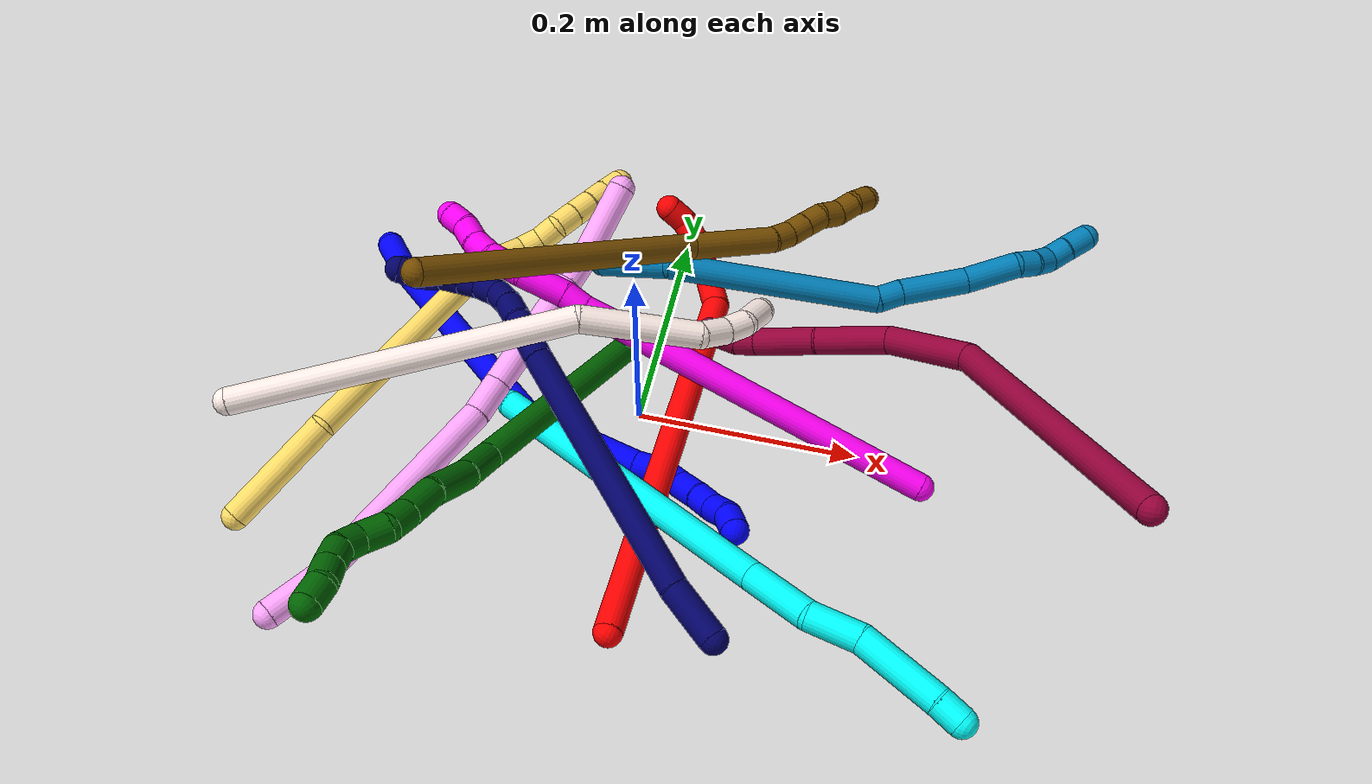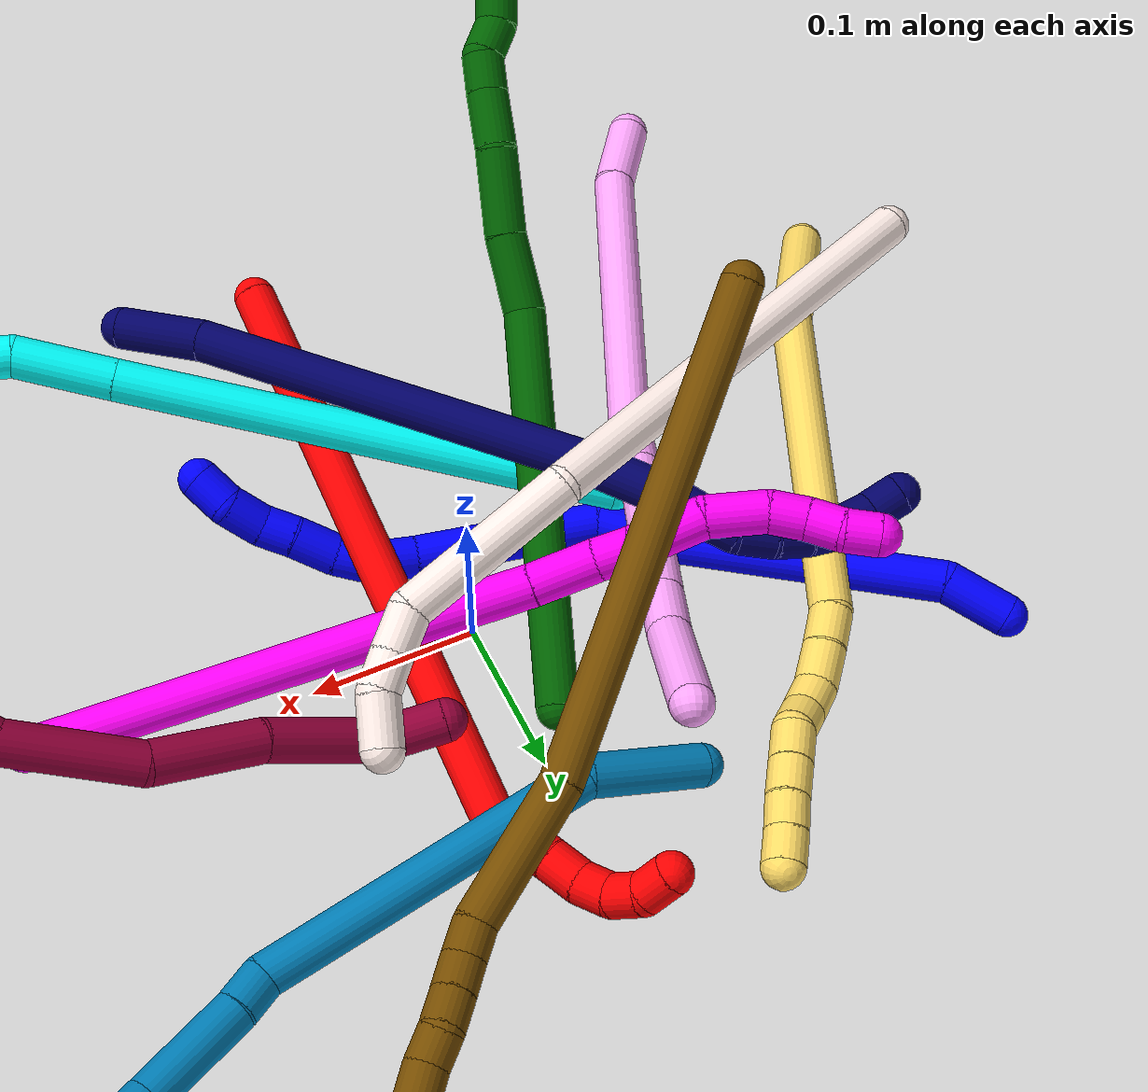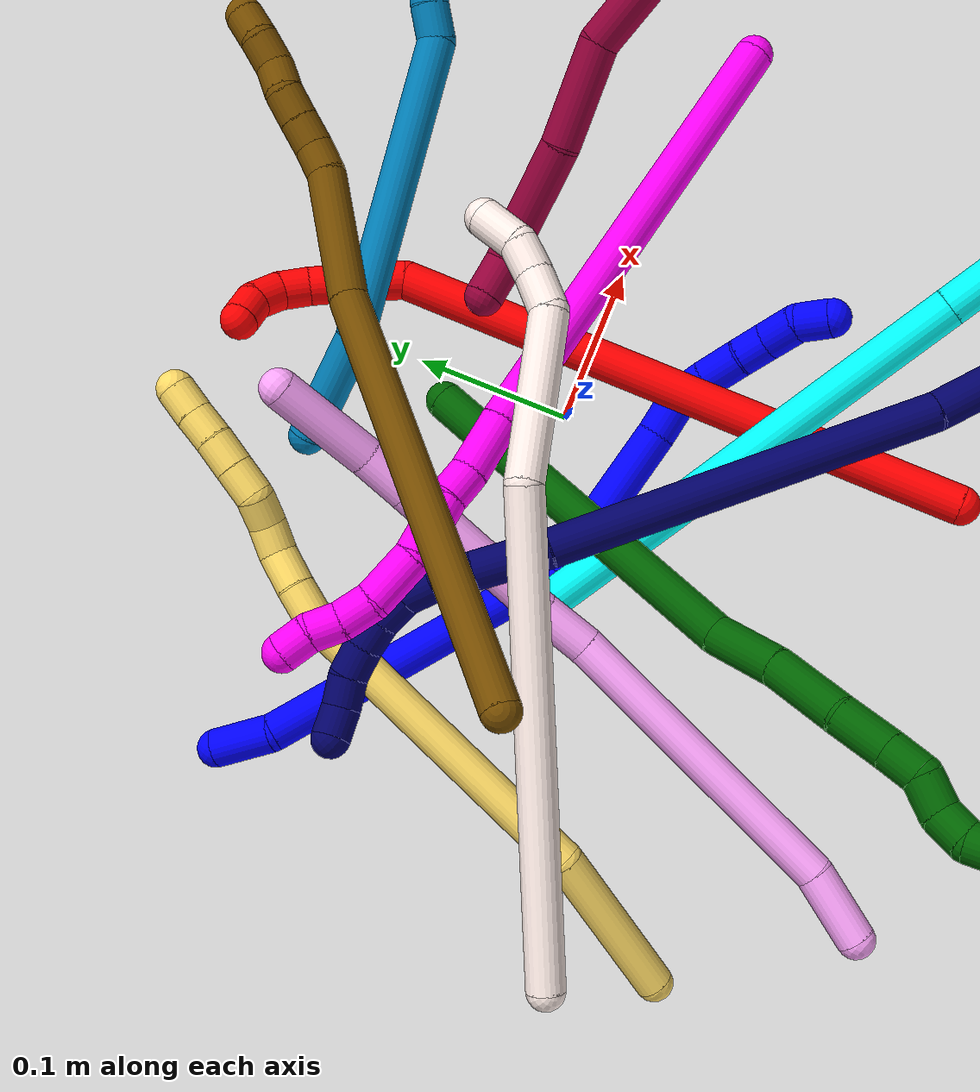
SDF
<sdf version="1.7">
 <world name="default">
  <plugin name="TubeGeneratorPlugin" filename="libtube_generator_plugin.so"/>
  <model name="photoneo_s_sensor">
   <static>1</static>
   <pose>0 0 2 1.57079 1.57079 3.14159</pose>
   <link name="link">
    <inertial><mass>0.1</mass></inertial>
    <sensor name="sensor" type="depth">
     <update_rate>30</update_rate>
     <camera>
      <horizontal_fov>1.22</horizontal_fov>
      <image><width>1920</width><height>1200</height><format>B8G8R8</format></image>
      <clip><near>0.1</near><far>4</far></clip>
      <depth_camera><output>points</output></depth_camera>
     </camera>
     <plugin name="camera_plugin" filename="libgazebo_ros_depth_camera.so">
      <baseline>0.2</baseline>
      <alwaysOn>1</alwaysOn>
      <updateRate>0.0</updateRate>
      <cameraName>camera_ir</cameraName>
      <imageTopicName>/camera/color/image_raw</imageTopicName>
      <cameraInfoTopicName>/camera/color/camera_info</cameraInfoTopicName>
      <depthImageTopicName>/camera/depth/image_raw</depthImageTopicName>
      <depthImageCameraInfoTopicName>/camera/depth/camera_info</depthImageCameraInfoTopicName>
      <pointCloudTopicName>/camera/depth/points</pointCloudTopicName>
      <frameName>fr_optical</frameName>
      <pointCloudCutoff>0.1</pointCloudCutoff>
      <pointCloudCutoffMax>2.0</pointCloudCutoffMax>
      <distortionK1>0</distortionK1>
      <distortionK2>0</distortionK2>
      <distortionK3>0</distortionK3>
      <distortionT1>0</distortionT1>
      <distortionT2>0</distortionT2>
      <CxPrime>0</CxPrime>
      <Cx>0</Cx>
      <Cy>0</Cy>
      <focalLength>0</focalLength>
      <hackBaseline>0</hackBaseline>
     </plugin>
    </sensor>
   </link>
  </model>
  <gravity>0 0 -9.8</gravity>
  <magnetic_field>6e-06 2.3e-05 -4.2e-05</magnetic_field>
  <atmosphere type="adiabatic"/>
  <physics name="default_physics" default="0" type="ode">
   <max_step_size>0.003</max_step_size>
   <real_time_factor>1</real_time_factor>
   <real_time_update_rate>1000</real_time_update_rate>
   <max_contacts>10000</max_contacts>
   <ode>
    <solver>
     <type>quick</type>
     <iters>100</iters>
     <sor>1.3</sor>
     <use_dynamic_moi_rescaling>0</use_dynamic_moi_rescaling>
    </solver>
    <constraints>
     <contact_max_correcting_vel>0</contact_max_correcting_vel>
     <contact_surface_layer>0.001</contact_surface_layer>
     <cfm>0</cfm>
     <erp>0.2</erp>
    </constraints>
   </ode>
  </physics>
  <scene><ambient>0.4 0.4 0.4 1</ambient><background>0.7 0.7 0.7 1</background><shadows>0</shadows></scene>
  <audio><device>default</device></audio>
  <spherical_coordinates>
   <surface_model>EARTH_WGS84</surface_model>
   <latitude_deg>0</latitude_deg>
   <longitude_deg>0</longitude_deg>
   <elevation>0</elevation>
   <heading_deg>0</heading_deg>
  </spherical_coordinates>
  <model name="bin">
   <static>1</static>
   <link name="bottom">
    <collision name="collision-bottom">
     <pose>0 0 -0.01 0 -0 0</pose>
     <geometry><box><size>0.8 0.6 0.02</size></box></geometry>
     <surface>
      <friction><ode><mu>100</mu><mu2>100</mu2></ode></friction>
      <contact><collide_bitmask>65535</collide_bitmask></contact>
     </surface>
    </collision>
   </link>
   <link name="west_wall">
    <collision name="collision-west_wall">
     <pose>-0.41 0 0.1 0 -0 0</pose>
     <geometry><box><size>0.02 0.6 0.2</size></box></geometry>
     <surface>
      <friction><ode><mu>100</mu><mu2>100</mu2></ode></friction>
      <contact><collide_bitmask>65535</collide_bitmask></contact>
     </surface>
    </collision>
   </link>
   <link name="east_wall">
    <collision name="collision-east_wall">
     <pose>0.41 0 0.1 0 -0 0</pose>
     <geometry><box><size>0.02 0.6 0.2</size></box></geometry>
     <surface>
      <friction><ode><mu>100</mu><mu2>100</mu2></ode></friction>
      <contact><collide_bitmask>65535</collide_bitmask></contact>
     </surface>
    </collision>
   </link>
   <link name="south_wall">
    <collision name="collision-south_wall">
     <pose>0 -0.31 0.1 0 -0 0</pose>
     <geometry><box><size>0.8 0.02 0.2</size></box></geometry>
     <surface>
      <friction><ode><mu>100</mu><mu2>100</mu2></ode></friction>
      <contact><collide_bitmask>65535</collide_bitmask></contact>
     </surface>
    </collision>
   </link>
   <link name="north_wall">
    <collision name="collision-north_wall">
     <pose>0 0.31 0.1 0 -0 0</pose>
     <geometry><box><size>0.8 0.02 0.2</size></box></geometry>
     <surface>
      <friction><ode><mu>100</mu><mu2>100</mu2></ode></friction>
      <contact><collide_bitmask>65535</collide_bitmask></contact>
     </surface>
    </collision>
   </link>
  </model>
  <model name="1">
   <static>0</static>
   <link name="1">
    <collision name="collision-cylinder-e_1_1_4">
     <pose>0.014006 0.000355 0.014058 -0.025251 0.783366 -0.01043</pose>
     <geometry><cylinder><radius>0.0125</radius><length>0.039695</length></cylinder></geometry>
     <surface>
      <friction><ode><mu>1.16</mu><mu2>1.16</mu2><slip1>0</slip1><slip2>0</slip2></ode></friction>
      <contact><ode><kp>1e+06</kp><kd>1</kd><max_vel>0</max_vel><min_depth>0.001</min_depth></ode></contact>
     </surface>
    </collision>
    <visual name="visual-cylinder-e_1_1_4">
     <pose>0.014006 0.000355 0.014058 -0.025251 0.783366 -0.01043</pose>
     <geometry><cylinder><radius>0.0125</radius><length>0.039695</length></cylinder></geometry>
     <material><ambient>0 0 1 1</ambient></material>
    </visual>
    <collision name="collision-cylinder-e_2_4_5">
     <pose>0.089215 -0.030558 0.082302 0.523384 0.774441 0.217588</pose>
     <geometry><cylinder><radius>0.0125</radius><length>0.175038</length></cylinder></geometry>
     <surface>
      <friction><ode><mu>1.16</mu><mu2>1.16</mu2><slip1>0</slip1><slip2>0</slip2></ode></friction>
      <contact><ode><kp>1e+06</kp><kd>1</kd><max_vel>0</max_vel><min_depth>0.001</min_depth></ode></contact>
     </surface>
    </collision>
    <visual name="visual-cylinder-e_2_4_5">
     <pose>0.089215 -0.030558 0.082302 0.523384 0.774441 0.217588</pose>
     <geometry><cylinder><radius>0.0125</radius><length>0.175038</length></cylinder></geometry>
     <material><ambient>0 0 1 1</ambient></material>
    </visual>
    <collision name="collision-cylinder-e_3_5_6">
     <pose>0.163448 -0.065194 0.147237 0.30358 0.85785 0.139682</pose>
     <geometry><cylinder><radius>0.0125</radius><length>0.034448</length></cylinder></geometry>
     <surface>
      <friction><ode><mu>1.16</mu><mu2>1.16</mu2><slip1>0</slip1><slip2>0</slip2></ode></friction>
      <contact><ode><kp>1e+06</kp><kd>1</kd><max_vel>0</max_vel><min_depth>0.001</min_depth></ode></contact>
     </surface>
    </collision>
    <visual name="visual-cylinder-e_3_5_6">
     <pose>0.163448 -0.065194 0.147237 0.30358 0.85785 0.139682</pose>
     <geometry><cylinder><radius>0.0125</radius><length>0.034448</length></cylinder></geometry>
     <material><ambient>0 0 1 1</ambient></material>
    </visual>
    <collision name="collision-cylinder-e_4_6_7">
     <pose>0.222959 -0.09494 0.170505 1.12773 1.00993 0.67253</pose>
     <geometry><cylinder><radius>0.0125</radius><length>0.109783</length></cylinder></geometry>
     <surface>
      <friction><ode><mu>1.16</mu><mu2>1.16</mu2><slip1>0</slip1><slip2>0</slip2></ode></friction>
      <contact><ode><kp>1e+06</kp><kd>1</kd><max_vel>0</max_vel><min_depth>0.001</min_depth></ode></contact>
     </surface>
    </collision>
    <visual name="visual-cylinder-e_4_6_7">
     <pose>0.222959 -0.09494 0.170505 1.12773 1.00993 0.67253</pose>
     <geometry><cylinder><radius>0.0125</radius><length>0.109783</length></cylinder></geometry>
     <material><ambient>0 0 1 1</ambient></material>
    </visual>
    <collision name="collision-cylinder-e_5_7_8">
     <pose>0.282149 -0.126117 0.184978 1.18383 1.18366 0.848945</pose>
     <geometry><cylinder><radius>0.0125</radius><length>0.027447</length></cylinder></geometry>
     <surface>
      <friction><ode><mu>1.16</mu><mu2>1.16</mu2><slip1>0</slip1><slip2>0</slip2></ode></friction>
      <contact><ode><kp>1e+06</kp><kd>1</kd><max_vel>0</max_vel><min_depth>0.001</min_depth></ode></contact>
     </surface>
    </collision>
    <visual name="visual-cylinder-e_5_7_8">
     <pose>0.282149 -0.126117 0.184978 1.18383 1.18366 0.848945</pose>
     <geometry><cylinder><radius>0.0125</radius><length>0.027447</length></cylinder></geometry>
     <material><ambient>0 0 1 1</ambient></material>
    </visual>
    <collision name="collision-cylinder-e_6_8_9">
     <pose>0.303941 -0.132624 0.191952 0.328146 1.04255 0.18958</pose>
     <geometry><cylinder><radius>0.0125</radius><length>0.021036</length></cylinder></geometry>
     <surface>
      <friction><ode><mu>1.16</mu><mu2>1.16</mu2><slip1>0</slip1><slip2>0</slip2></ode></friction>
      <contact><ode><kp>1e+06</kp><kd>1</kd><max_vel>0</max_vel><min_depth>0.001</min_depth></ode></contact>
     </surface>
    </collision>
    <visual name="visual-cylinder-e_6_8_9">
     <pose>0.303941 -0.132624 0.191952 0.328146 1.04255 0.18958</pose>
     <geometry><cylinder><radius>0.0125</radius><length>0.021036</length></cylinder></geometry>
     <material><ambient>0 0 1 1</ambient></material>
    </visual>
    <collision name="collision-cylinder-e_7_9_10">
     <pose>0.324826 -0.133435 0.203039 -0.146747 1.09143 -0.089209</pose>
     <geometry><cylinder><radius>0.0125</radius><length>0.026599</length></cylinder></geometry>
     <surface>
      <friction><ode><mu>1.16</mu><mu2>1.16</mu2><slip1>0</slip1><slip2>0</slip2></ode></friction>
      <contact><ode><kp>1e+06</kp><kd>1</kd><max_vel>0</max_vel><min_depth>0.001</min_depth></ode></contact>
     </surface>
    </collision>
    <visual name="visual-cylinder-e_7_9_10">
     <pose>0.324826 -0.133435 0.203039 -0.146747 1.09143 -0.089209</pose>
     <geometry><cylinder><radius>0.0125</radius><length>0.026599</length></cylinder></geometry>
     <material><ambient>0 0 1 1</ambient></material>
    </visual>
    <collision name="collision-cylinder-e_8_10_11">
     <pose>0.345293 -0.133079 0.214321 0.103287 1.02676 0.058269</pose>
     <geometry><cylinder><radius>0.0125</radius><length>0.020258</length></cylinder></geometry>
     <surface>
      <friction><ode><mu>1.16</mu><mu2>1.16</mu2><slip1>0</slip1><slip2>0</slip2></ode></friction>
      <contact><ode><kp>1e+06</kp><kd>1</kd><max_vel>0</max_vel><min_depth>0.001</min_depth></ode></contact>
     </surface>
    </collision>
    <visual name="visual-cylinder-e_8_10_11">
     <pose>0.345293 -0.133079 0.214321 0.103287 1.02676 0.058269</pose>
     <geometry><cylinder><radius>0.0125</radius><length>0.020258</length></cylinder></geometry>
     <material><ambient>0 0 1 1</ambient></material>
    </visual>
    <collision name="collision-cylinder-e_9_11_12">
     <pose>0.364605 -0.130731 0.224284 -0.546473 1.08967 -0.336458</pose>
     <geometry><cylinder><radius>0.0125</radius><length>0.024018</length></cylinder></geometry>
     <surface>
      <friction><ode><mu>1.16</mu><mu2>1.16</mu2><slip1>0</slip1><slip2>0</slip2></ode></friction>
      <contact><ode><kp>1e+06</kp><kd>1</kd><max_vel>0</max_vel><min_depth>0.001</min_depth></ode></contact>
     </surface>
    </collision>
    <visual name="visual-cylinder-e_9_11_12">
     <pose>0.364605 -0.130731 0.224284 -0.546473 1.08967 -0.336458</pose>
     <geometry><cylinder><radius>0.0125</radius><length>0.024018</length></cylinder></geometry>
     <material><ambient>0 0 1 1</ambient></material>
    </visual>
    <collision name="collision-cylinder-e_10_12_2">
     <pose>0.382175 -0.125233 0.236952 -0.31836 0.693014 -0.115803</pose>
     <geometry><cylinder><radius>0.0125</radius><length>0.021677</length></cylinder></geometry>
     <surface>
      <friction><ode><mu>1.16</mu><mu2>1.16</mu2><slip1>0</slip1><slip2>0</slip2></ode></friction>
      <contact><ode><kp>1e+06</kp><kd>1</kd><max_vel>0</max_vel><min_depth>0.001</min_depth></ode></contact>
     </surface>
    </collision>
    <visual name="visual-cylinder-e_10_12_2">
     <pose>0.382175 -0.125233 0.236952 -0.31836 0.693014 -0.115803</pose>
     <geometry><cylinder><radius>0.0125</radius><length>0.021677</length></cylinder></geometry>
     <material><ambient>0 0 1 1</ambient></material>
    </visual>
    <collision name="collision-sphere-2">
     <pose>0.389099 -0.122623 0.244871 0 -0 0</pose>
     <geometry><sphere><radius>0.0125</radius></sphere></geometry>
     <surface>
      <friction><ode><mu>1.16</mu><mu2>1.16</mu2><slip1>0</slip1><slip2>0</slip2></ode></friction>
      <contact><ode><kp>1e+06</kp><kd>1</kd><max_vel>0</max_vel><min_depth>0.001</min_depth></ode></contact>
     </surface>
    </collision>
    <visual name="visual-sphere-2">
     <pose>0.389099 -0.122623 0.244871 0 -0 0</pose>
     <geometry><sphere><radius>0.0125</radius></sphere></geometry>
     <material><ambient>0 0 1 1</ambient></material>
    </visual>
    <collision name="collision-sphere-12">
     <pose>0.375251 -0.127843 0.229032 0 -0 0</pose>
     <geometry><sphere><radius>0.0125</radius></sphere></geometry>
     <surface>
      <friction><ode><mu>1.16</mu><mu2>1.16</mu2><slip1>0</slip1><slip2>0</slip2></ode></friction>
      <contact><ode><kp>1e+06</kp><kd>1</kd><max_vel>0</max_vel><min_depth>0.001</min_depth></ode></contact>
     </surface>
    </collision>
    <visual name="visual-sphere-12">
     <pose>0.375251 -0.127843 0.229032 0 -0 0</pose>
     <geometry><sphere><radius>0.0125</radius></sphere></geometry>
     <material><ambient>0 0 1 1</ambient></material>
    </visual>
    <collision name="collision-sphere-11">
     <pose>0.353959 -0.133619 0.219536 0 -0 0</pose>
     <geometry><sphere><radius>0.0125</radius></sphere></geometry>
     <surface>
      <friction><ode><mu>1.16</mu><mu2>1.16</mu2><slip1>0</slip1><slip2>0</slip2></ode></friction>
      <contact><ode><kp>1e+06</kp><kd>1</kd><max_vel>0</max_vel><min_depth>0.001</min_depth></ode></contact>
     </surface>
    </collision>
    <visual name="visual-sphere-11">
     <pose>0.353959 -0.133619 0.219536 0 -0 0</pose>
     <geometry><sphere><radius>0.0125</radius></sphere></geometry>
     <material><ambient>0 0 1 1</ambient></material>
    </visual>
    <collision name="collision-sphere-10">
     <pose>0.336626 -0.132538 0.209107 0 -0 0</pose>
     <geometry><sphere><radius>0.0125</radius></sphere></geometry>
     <surface>
      <friction><ode><mu>1.16</mu><mu2>1.16</mu2><slip1>0</slip1><slip2>0</slip2></ode></friction>
      <contact><ode><kp>1e+06</kp><kd>1</kd><max_vel>0</max_vel><min_depth>0.001</min_depth></ode></contact>
     </surface>
    </collision>
    <visual name="visual-sphere-10">
     <pose>0.336626 -0.132538 0.209107 0 -0 0</pose>
     <geometry><sphere><radius>0.0125</radius></sphere></geometry>
     <material><ambient>0 0 1 1</ambient></material>
    </visual>
    <collision name="collision-sphere-9">
     <pose>0.313025 -0.134332 0.19697 0 -0 0</pose>
     <geometry><sphere><radius>0.0125</radius></sphere></geometry>
     <surface>
      <friction><ode><mu>1.16</mu><mu2>1.16</mu2><slip1>0</slip1><slip2>0</slip2></ode></friction>
      <contact><ode><kp>1e+06</kp><kd>1</kd><max_vel>0</max_vel><min_depth>0.001</min_depth></ode></contact>
     </surface>
    </collision>
    <visual name="visual-sphere-9">
     <pose>0.313025 -0.134332 0.19697 0 -0 0</pose>
     <geometry><sphere><radius>0.0125</radius></sphere></geometry>
     <material><ambient>0 0 1 1</ambient></material>
    </visual>
    <collision name="collision-sphere-4">
     <pose>0.028012 0.00071 0.028117 0 -0 0</pose>
     <geometry><sphere><radius>0.0125</radius></sphere></geometry>
     <surface>
      <friction><ode><mu>1.16</mu><mu2>1.16</mu2><slip1>0</slip1><slip2>0</slip2></ode></friction>
      <contact><ode><kp>1e+06</kp><kd>1</kd><max_vel>0</max_vel><min_depth>0.001</min_depth></ode></contact>
     </surface>
    </collision>
    <visual name="visual-sphere-4">
     <pose>0.028012 0.00071 0.028117 0 -0 0</pose>
     <geometry><sphere><radius>0.0125</radius></sphere></geometry>
     <material><ambient>0 0 1 1</ambient></material>
    </visual>
    <collision name="collision-sphere-1">
     <geometry><sphere><radius>0.0125</radius></sphere></geometry>
     <surface>
      <friction><ode><mu>1.16</mu><mu2>1.16</mu2><slip1>0</slip1><slip2>0</slip2></ode></friction>
      <contact><ode><kp>1e+06</kp><kd>1</kd><max_vel>0</max_vel><min_depth>0.001</min_depth></ode></contact>
     </surface>
    </collision>
    <visual name="visual-sphere-1">
     <geometry><sphere><radius>0.0125</radius></sphere></geometry>
     <material><ambient>0 0 1 1</ambient></material>
    </visual>
    <collision name="collision-sphere-8">
     <pose>0.294857 -0.130915 0.186934 0 -0 0</pose>
     <geometry><sphere><radius>0.0125</radius></sphere></geometry>
     <surface>
      <friction><ode><mu>1.16</mu><mu2>1.16</mu2><slip1>0</slip1><slip2>0</slip2></ode></friction>
      <contact><ode><kp>1e+06</kp><kd>1</kd><max_vel>0</max_vel><min_depth>0.001</min_depth></ode></contact>
     </surface>
    </collision>
    <visual name="visual-sphere-8">
     <pose>0.294857 -0.130915 0.186934 0 -0 0</pose>
     <geometry><sphere><radius>0.0125</radius></sphere></geometry>
     <material><ambient>0 0 1 1</ambient></material>
    </visual>
    <collision name="collision-sphere-5">
     <pose>0.150419 -0.061826 0.136487 0 -0 0</pose>
     <geometry><sphere><radius>0.0125</radius></sphere></geometry>
     <surface>
      <friction><ode><mu>1.16</mu><mu2>1.16</mu2><slip1>0</slip1><slip2>0</slip2></ode></friction>
      <contact><ode><kp>1e+06</kp><kd>1</kd><max_vel>0</max_vel><min_depth>0.001</min_depth></ode></contact>
     </surface>
    </collision>
    <visual name="visual-sphere-5">
     <pose>0.150419 -0.061826 0.136487 0 -0 0</pose>
     <geometry><sphere><radius>0.0125</radius></sphere></geometry>
     <material><ambient>0 0 1 1</ambient></material>
    </visual>
    <collision name="collision-sphere-6">
     <pose>0.176477 -0.068562 0.157988 0 -0 0</pose>
     <geometry><sphere><radius>0.0125</radius></sphere></geometry>
     <surface>
      <friction><ode><mu>1.16</mu><mu2>1.16</mu2><slip1>0</slip1><slip2>0</slip2></ode></friction>
      <contact><ode><kp>1e+06</kp><kd>1</kd><max_vel>0</max_vel><min_depth>0.001</min_depth></ode></contact>
     </surface>
    </collision>
    <visual name="visual-sphere-6">
     <pose>0.176477 -0.068562 0.157988 0 -0 0</pose>
     <geometry><sphere><radius>0.0125</radius></sphere></geometry>
     <material><ambient>0 0 1 1</ambient></material>
    </visual>
    <collision name="collision-sphere-7">
     <pose>0.269441 -0.121319 0.183023 0 -0 0</pose>
     <geometry><sphere><radius>0.0125</radius></sphere></geometry>
     <surface>
      <friction><ode><mu>1.16</mu><mu2>1.16</mu2><slip1>0</slip1><slip2>0</slip2></ode></friction>
      <contact><ode><kp>1e+06</kp><kd>1</kd><max_vel>0</max_vel><min_depth>0.001</min_depth></ode></contact>
     </surface>
    </collision>
    <visual name="visual-sphere-7">
     <pose>0.269441 -0.121319 0.183023 0 -0 0</pose>
     <geometry><sphere><radius>0.0125</radius></sphere></geometry>
     <material><ambient>0 0 1 1</ambient></material>
    </visual>
    <inertial>
     <pose>0.186188 -0.072709 0.136271 0 -0 0</pose>
     <mass>0.5</mass>
     <inertia>
      <ixx>0.000517</ixx>
      <ixy>0</ixy>
      <ixz>0</ixz>
      <iyy>0.000633</iyy>
      <iyz>0</iyz>
      <izz>-0.000196</izz>
     </inertia>
    </inertial>
   </link>
   <pose>-0.28162 0.129386 0.013076 1.76441 -0.514844 -0.103251</pose>
  </model>
  <model name="2">
   <static>0</static>
   <link name="2">
    <collision name="collision-cylinder-e_1_1_4">
     <pose>0.033708 0.144693 0.116862 -0.891404 0.179288 -0.085835</pose>
     <geometry><cylinder><radius>0.0125</radius><length>0.378043</length></cylinder></geometry>
     <surface>
      <friction><ode><mu>1.16</mu><mu2>1.16</mu2><slip1>0</slip1><slip2>0</slip2></ode></friction>
      <contact><ode><kp>1e+06</kp><kd>1</kd><max_vel>0</max_vel><min_depth>0.001</min_depth></ode></contact>
     </surface>
    </collision>
    <visual name="visual-cylinder-e_1_1_4">
     <pose>0.033708 0.144693 0.116862 -0.891404 0.179288 -0.085835</pose>
     <geometry><cylinder><radius>0.0125</radius><length>0.378043</length></cylinder></geometry>
     <material><ambient>1 0 0 1</ambient></material>
    </visual>
    <collision name="collision-cylinder-e_2_4_5">
     <pose>0.061733 0.305767 0.243722 -1.02284 -0.287892 0.162339</pose>
     <geometry><cylinder><radius>0.0125</radius><length>0.040029</length></cylinder></geometry>
     <surface>
      <friction><ode><mu>1.16</mu><mu2>1.16</mu2><slip1>0</slip1><slip2>0</slip2></ode></friction>
      <contact><ode><kp>1e+06</kp><kd>1</kd><max_vel>0</max_vel><min_depth>0.001</min_depth></ode></contact>
     </surface>
    </collision>
    <visual name="visual-cylinder-e_2_4_5">
     <pose>0.061733 0.305767 0.243722 -1.02284 -0.287892 0.162339</pose>
     <geometry><cylinder><radius>0.0125</radius><length>0.040029</length></cylinder></geometry>
     <material><ambient>1 0 0 1</ambient></material>
    </visual>
    <collision name="collision-cylinder-e_3_5_6">
     <pose>0.053473 0.331629 0.258371 -1.11464 -0.239437 0.149659</pose>
     <geometry><cylinder><radius>0.0125</radius><length>0.02174</length></cylinder></geometry>
     <surface>
      <friction><ode><mu>1.16</mu><mu2>1.16</mu2><slip1>0</slip1><slip2>0</slip2></ode></friction>
      <contact><ode><kp>1e+06</kp><kd>1</kd><max_vel>0</max_vel><min_depth>0.001</min_depth></ode></contact>
     </surface>
    </collision>
    <visual name="visual-cylinder-e_3_5_6">
     <pose>0.053473 0.331629 0.258371 -1.11464 -0.239437 0.149659</pose>
     <geometry><cylinder><radius>0.0125</radius><length>0.02174</length></cylinder></geometry>
     <material><ambient>1 0 0 1</ambient></material>
    </visual>
    <collision name="collision-cylinder-e_4_6_7">
     <pose>0.046173 0.348214 0.268304 -0.931674 -0.489966 0.250063</pose>
     <geometry><cylinder><radius>0.0125</radius><length>0.020066</length></cylinder></geometry>
     <surface>
      <friction><ode><mu>1.16</mu><mu2>1.16</mu2><slip1>0</slip1><slip2>0</slip2></ode></friction>
      <contact><ode><kp>1e+06</kp><kd>1</kd><max_vel>0</max_vel><min_depth>0.001</min_depth></ode></contact>
     </surface>
    </collision>
    <visual name="visual-cylinder-e_4_6_7">
     <pose>0.046173 0.348214 0.268304 -0.931674 -0.489966 0.250063</pose>
     <geometry><cylinder><radius>0.0125</radius><length>0.020066</length></cylinder></geometry>
     <material><ambient>1 0 0 1</ambient></material>
    </visual>
    <collision name="collision-cylinder-e_5_7_8">
     <pose>0.033717 0.359426 0.278458 -0.700093 -0.881581 0.341105</pose>
     <geometry><cylinder><radius>0.0125</radius><length>0.020044</length></cylinder></geometry>
     <surface>
      <friction><ode><mu>1.16</mu><mu2>1.16</mu2><slip1>0</slip1><slip2>0</slip2></ode></friction>
      <contact><ode><kp>1e+06</kp><kd>1</kd><max_vel>0</max_vel><min_depth>0.001</min_depth></ode></contact>
     </surface>
    </collision>
    <visual name="visual-cylinder-e_5_7_8">
     <pose>0.033717 0.359426 0.278458 -0.700093 -0.881581 0.341105</pose>
     <geometry><cylinder><radius>0.0125</radius><length>0.020044</length></cylinder></geometry>
     <material><ambient>1 0 0 1</ambient></material>
    </visual>
    <collision name="collision-cylinder-e_6_8_2">
     <pose>0.016164 0.364057 0.285354 -0.254002 -1.36119 0.206033</pose>
     <geometry><cylinder><radius>0.0125</radius><length>0.020077</length></cylinder></geometry>
     <surface>
      <friction><ode><mu>1.16</mu><mu2>1.16</mu2><slip1>0</slip1><slip2>0</slip2></ode></friction>
      <contact><ode><kp>1e+06</kp><kd>1</kd><max_vel>0</max_vel><min_depth>0.001</min_depth></ode></contact>
     </surface>
    </collision>
    <visual name="visual-cylinder-e_6_8_2">
     <pose>0.016164 0.364057 0.285354 -0.254002 -1.36119 0.206033</pose>
     <geometry><cylinder><radius>0.0125</radius><length>0.020077</length></cylinder></geometry>
     <material><ambient>1 0 0 1</ambient></material>
    </visual>
    <collision name="collision-sphere-2">
     <pose>0.006345 0.364582 0.287376 0 -0 0</pose>
     <geometry><sphere><radius>0.0125</radius></sphere></geometry>
     <surface>
      <friction><ode><mu>1.16</mu><mu2>1.16</mu2><slip1>0</slip1><slip2>0</slip2></ode></friction>
      <contact><ode><kp>1e+06</kp><kd>1</kd><max_vel>0</max_vel><min_depth>0.001</min_depth></ode></contact>
     </surface>
    </collision>
    <visual name="visual-sphere-2">
     <pose>0.006345 0.364582 0.287376 0 -0 0</pose>
     <geometry><sphere><radius>0.0125</radius></sphere></geometry>
     <material><ambient>1 0 0 1</ambient></material>
    </visual>
    <collision name="collision-sphere-4">
     <pose>0.067416 0.289386 0.233725 0 -0 0</pose>
     <geometry><sphere><radius>0.0125</radius></sphere></geometry>
     <surface>
      <friction><ode><mu>1.16</mu><mu2>1.16</mu2><slip1>0</slip1><slip2>0</slip2></ode></friction>
      <contact><ode><kp>1e+06</kp><kd>1</kd><max_vel>0</max_vel><min_depth>0.001</min_depth></ode></contact>
     </surface>
    </collision>
    <visual name="visual-sphere-4">
     <pose>0.067416 0.289386 0.233725 0 -0 0</pose>
     <geometry><sphere><radius>0.0125</radius></sphere></geometry>
     <material><ambient>1 0 0 1</ambient></material>
    </visual>
    <collision name="collision-sphere-1">
     <geometry><sphere><radius>0.0125</radius></sphere></geometry>
     <surface>
      <friction><ode><mu>1.16</mu><mu2>1.16</mu2><slip1>0</slip1><slip2>0</slip2></ode></friction>
      <contact><ode><kp>1e+06</kp><kd>1</kd><max_vel>0</max_vel><min_depth>0.001</min_depth></ode></contact>
     </surface>
    </collision>
    <visual name="visual-sphere-1">
     <geometry><sphere><radius>0.0125</radius></sphere></geometry>
     <material><ambient>1 0 0 1</ambient></material>
    </visual>
    <collision name="collision-sphere-8">
     <pose>0.025983 0.363532 0.283333 0 -0 0</pose>
     <geometry><sphere><radius>0.0125</radius></sphere></geometry>
     <surface>
      <friction><ode><mu>1.16</mu><mu2>1.16</mu2><slip1>0</slip1><slip2>0</slip2></ode></friction>
      <contact><ode><kp>1e+06</kp><kd>1</kd><max_vel>0</max_vel><min_depth>0.001</min_depth></ode></contact>
     </surface>
    </collision>
    <visual name="visual-sphere-8">
     <pose>0.025983 0.363532 0.283333 0 -0 0</pose>
     <geometry><sphere><radius>0.0125</radius></sphere></geometry>
     <material><ambient>1 0 0 1</ambient></material>
    </visual>
    <collision name="collision-sphere-5">
     <pose>0.056051 0.322148 0.25372 0 -0 0</pose>
     <geometry><sphere><radius>0.0125</radius></sphere></geometry>
     <surface>
      <friction><ode><mu>1.16</mu><mu2>1.16</mu2><slip1>0</slip1><slip2>0</slip2></ode></friction>
      <contact><ode><kp>1e+06</kp><kd>1</kd><max_vel>0</max_vel><min_depth>0.001</min_depth></ode></contact>
     </surface>
    </collision>
    <visual name="visual-sphere-5">
     <pose>0.056051 0.322148 0.25372 0 -0 0</pose>
     <geometry><sphere><radius>0.0125</radius></sphere></geometry>
     <material><ambient>1 0 0 1</ambient></material>
    </visual>
    <collision name="collision-sphere-6">
     <pose>0.050895 0.341109 0.263023 0 -0 0</pose>
     <geometry><sphere><radius>0.0125</radius></sphere></geometry>
     <surface>
      <friction><ode><mu>1.16</mu><mu2>1.16</mu2><slip1>0</slip1><slip2>0</slip2></ode></friction>
      <contact><ode><kp>1e+06</kp><kd>1</kd><max_vel>0</max_vel><min_depth>0.001</min_depth></ode></contact>
     </surface>
    </collision>
    <visual name="visual-sphere-6">
     <pose>0.050895 0.341109 0.263023 0 -0 0</pose>
     <geometry><sphere><radius>0.0125</radius></sphere></geometry>
     <material><ambient>1 0 0 1</ambient></material>
    </visual>
    <collision name="collision-sphere-7">
     <pose>0.041452 0.355319 0.273584 0 -0 0</pose>
     <geometry><sphere><radius>0.0125</radius></sphere></geometry>
     <surface>
      <friction><ode><mu>1.16</mu><mu2>1.16</mu2><slip1>0</slip1><slip2>0</slip2></ode></friction>
      <contact><ode><kp>1e+06</kp><kd>1</kd><max_vel>0</max_vel><min_depth>0.001</min_depth></ode></contact>
     </surface>
    </collision>
    <visual name="visual-sphere-7">
     <pose>0.041452 0.355319 0.273584 0 -0 0</pose>
     <geometry><sphere><radius>0.0125</radius></sphere></geometry>
     <material><ambient>1 0 0 1</ambient></material>
    </visual>
    <inertial>
     <pose>0.036607 0.191301 0.152493 0 -0 0</pose>
     <mass>0.5</mass>
     <inertia>
      <ixx>0.00406</ixx>
      <ixy>0</ixy>
      <ixz>0</ixz>
      <iyy>0.002539</iyy>
      <iyz>0</iyz>
      <izz>-0.004244</izz>
     </inertia>
    </inertial>
   </link>
   <pose>0.035961 -0.245626 0.065422 -0.726664 0.592273 0.103583</pose>
  </model>
  <model name="3">
   <static>0</static>
   <link name="3">
    <collision name="collision-cylinder-e_1_1_4">
     <pose>0.012003 0.006952 0.148515 -0.046779 0.080555 -0.001885</pose>
     <geometry><cylinder><radius>0.0125</radius><length>0.298323</length></cylinder></geometry>
     <surface>
      <friction><ode><mu>1.16</mu><mu2>1.16</mu2><slip1>0</slip1><slip2>0</slip2></ode></friction>
      <contact><ode><kp>1e+06</kp><kd>1</kd><max_vel>0</max_vel><min_depth>0.001</min_depth></ode></contact>
     </surface>
    </collision>
    <visual name="visual-cylinder-e_1_1_4">
     <pose>0.012003 0.006952 0.148515 -0.046779 0.080555 -0.001885</pose>
     <geometry><cylinder><radius>0.0125</radius><length>0.298323</length></cylinder></geometry>
     <material><ambient>0.003922 1 0.996078 1</ambient></material>
    </visual>
    <collision name="collision-cylinder-e_2_4_5">
     <pose>0.026843 0.015516 0.326698 -0.054253 0.095228 -0.002586</pose>
     <geometry><cylinder><radius>0.0125</radius><length>0.059694</length></cylinder></geometry>
     <surface>
      <friction><ode><mu>1.16</mu><mu2>1.16</mu2><slip1>0</slip1><slip2>0</slip2></ode></friction>
      <contact><ode><kp>1e+06</kp><kd>1</kd><max_vel>0</max_vel><min_depth>0.001</min_depth></ode></contact>
     </surface>
    </collision>
    <visual name="visual-cylinder-e_2_4_5">
     <pose>0.026843 0.015516 0.326698 -0.054253 0.095228 -0.002586</pose>
     <geometry><cylinder><radius>0.0125</radius><length>0.059694</length></cylinder></geometry>
     <material><ambient>0.003922 1 0.996078 1</ambient></material>
    </visual>
    <collision name="collision-cylinder-e_3_5_6">
     <pose>0.030885 0.010601 0.377937 0.293811 0.053367 0.007899</pose>
     <geometry><cylinder><radius>0.0125</radius><length>0.045137</length></cylinder></geometry>
     <surface>
      <friction><ode><mu>1.16</mu><mu2>1.16</mu2><slip1>0</slip1><slip2>0</slip2></ode></friction>
      <contact><ode><kp>1e+06</kp><kd>1</kd><max_vel>0</max_vel><min_depth>0.001</min_depth></ode></contact>
     </surface>
    </collision>
    <visual name="visual-cylinder-e_3_5_6">
     <pose>0.030885 0.010601 0.377937 0.293811 0.053367 0.007899</pose>
     <geometry><cylinder><radius>0.0125</radius><length>0.045137</length></cylinder></geometry>
     <material><ambient>0.003922 1 0.996078 1</ambient></material>
    </visual>
    <collision name="collision-cylinder-e_4_6_7">
     <pose>0.028613 0.002345 0.436431 0.046783 -0.093758 -0.002195</pose>
     <geometry><cylinder><radius>0.0125</radius><length>0.074254</length></cylinder></geometry>
     <surface>
      <friction><ode><mu>1.16</mu><mu2>1.16</mu2><slip1>0</slip1><slip2>0</slip2></ode></friction>
      <contact><ode><kp>1e+06</kp><kd>1</kd><max_vel>0</max_vel><min_depth>0.001</min_depth></ode></contact>
     </surface>
    </collision>
    <visual name="visual-cylinder-e_4_6_7">
     <pose>0.028613 0.002345 0.436431 0.046783 -0.093758 -0.002195</pose>
     <geometry><cylinder><radius>0.0125</radius><length>0.074254</length></cylinder></geometry>
     <material><ambient>0.003922 1 0.996078 1</ambient></material>
    </visual>
    <collision name="collision-cylinder-e_5_7_2">
     <pose>0.022543 -0.000637 0.484277 0.11431 -0.231736 -0.013319</pose>
     <geometry><cylinder><radius>0.0125</radius><length>0.022592</length></cylinder></geometry>
     <surface>
      <friction><ode><mu>1.16</mu><mu2>1.16</mu2><slip1>0</slip1><slip2>0</slip2></ode></friction>
      <contact><ode><kp>1e+06</kp><kd>1</kd><max_vel>0</max_vel><min_depth>0.001</min_depth></ode></contact>
     </surface>
    </collision>
    <visual name="visual-cylinder-e_5_7_2">
     <pose>0.022543 -0.000637 0.484277 0.11431 -0.231736 -0.013319</pose>
     <geometry><cylinder><radius>0.0125</radius><length>0.022592</length></cylinder></geometry>
     <material><ambient>0.003922 1 0.996078 1</ambient></material>
    </visual>
    <collision name="collision-sphere-2">
     <pose>0.019949 -0.001891 0.495199 0 -0 0</pose>
     <geometry><sphere><radius>0.0125</radius></sphere></geometry>
     <surface>
      <friction><ode><mu>1.16</mu><mu2>1.16</mu2><slip1>0</slip1><slip2>0</slip2></ode></friction>
      <contact><ode><kp>1e+06</kp><kd>1</kd><max_vel>0</max_vel><min_depth>0.001</min_depth></ode></contact>
     </surface>
    </collision>
    <visual name="visual-sphere-2">
     <pose>0.019949 -0.001891 0.495199 0 -0 0</pose>
     <geometry><sphere><radius>0.0125</radius></sphere></geometry>
     <material><ambient>0.003922 1 0.996078 1</ambient></material>
    </visual>
    <collision name="collision-sphere-7">
     <pose>0.025137 0.000617 0.473355 0 -0 0</pose>
     <geometry><sphere><radius>0.0125</radius></sphere></geometry>
     <surface>
      <friction><ode><mu>1.16</mu><mu2>1.16</mu2><slip1>0</slip1><slip2>0</slip2></ode></friction>
      <contact><ode><kp>1e+06</kp><kd>1</kd><max_vel>0</max_vel><min_depth>0.001</min_depth></ode></contact>
     </surface>
    </collision>
    <visual name="visual-sphere-7">
     <pose>0.025137 0.000617 0.473355 0 -0 0</pose>
     <geometry><sphere><radius>0.0125</radius></sphere></geometry>
     <material><ambient>0.003922 1 0.996078 1</ambient></material>
    </visual>
    <collision name="collision-sphere-6">
     <pose>0.032089 0.004074 0.399507 0 -0 0</pose>
     <geometry><sphere><radius>0.0125</radius></sphere></geometry>
     <surface>
      <friction><ode><mu>1.16</mu><mu2>1.16</mu2><slip1>0</slip1><slip2>0</slip2></ode></friction>
      <contact><ode><kp>1e+06</kp><kd>1</kd><max_vel>0</max_vel><min_depth>0.001</min_depth></ode></contact>
     </surface>
    </collision>
    <visual name="visual-sphere-6">
     <pose>0.032089 0.004074 0.399507 0 -0 0</pose>
     <geometry><sphere><radius>0.0125</radius></sphere></geometry>
     <material><ambient>0.003922 1 0.996078 1</ambient></material>
    </visual>
    <collision name="collision-sphere-5">
     <pose>0.029681 0.017127 0.356366 0 -0 0</pose>
     <geometry><sphere><radius>0.0125</radius></sphere></geometry>
     <surface>
      <friction><ode><mu>1.16</mu><mu2>1.16</mu2><slip1>0</slip1><slip2>0</slip2></ode></friction>
      <contact><ode><kp>1e+06</kp><kd>1</kd><max_vel>0</max_vel><min_depth>0.001</min_depth></ode></contact>
     </surface>
    </collision>
    <visual name="visual-sphere-5">
     <pose>0.029681 0.017127 0.356366 0 -0 0</pose>
     <geometry><sphere><radius>0.0125</radius></sphere></geometry>
     <material><ambient>0.003922 1 0.996078 1</ambient></material>
    </visual>
    <collision name="collision-sphere-1">
     <geometry><sphere><radius>0.0125</radius></sphere></geometry>
     <surface>
      <friction><ode><mu>1.16</mu><mu2>1.16</mu2><slip1>0</slip1><slip2>0</slip2></ode></friction>
      <contact><ode><kp>1e+06</kp><kd>1</kd><max_vel>0</max_vel><min_depth>0.001</min_depth></ode></contact>
     </surface>
    </collision>
    <visual name="visual-sphere-1">
     <geometry><sphere><radius>0.0125</radius></sphere></geometry>
     <material><ambient>0.003922 1 0.996078 1</ambient></material>
    </visual>
    <collision name="collision-sphere-4">
     <pose>0.024005 0.013905 0.29703 0 -0 0</pose>
     <geometry><sphere><radius>0.0125</radius></sphere></geometry>
     <surface>
      <friction><ode><mu>1.16</mu><mu2>1.16</mu2><slip1>0</slip1><slip2>0</slip2></ode></friction>
      <contact><ode><kp>1e+06</kp><kd>1</kd><max_vel>0</max_vel><min_depth>0.001</min_depth></ode></contact>
     </surface>
    </collision>
    <visual name="visual-sphere-4">
     <pose>0.024005 0.013905 0.29703 0 -0 0</pose>
     <geometry><sphere><radius>0.0125</radius></sphere></geometry>
     <material><ambient>0.003922 1 0.996078 1</ambient></material>
    </visual>
    <inertial>
     <pose>0.018422 0.007277 0.248428 0 -0 0</pose>
     <mass>0.5</mass>
     <inertia>
      <ixx>0.002282</ixx>
      <ixy>0</ixy>
      <ixz>0</ixz>
      <iyy>0.002285</iyy>
      <iyz>0</iyz>
      <izz>-0.000239</izz>
     </inertia>
    </inertial>
   </link>
   <pose>-0.108725 -0.036326 0.036052 1.28336 -1.13413 1.29592</pose>
  </model>
  <model name="4">
   <static>0</static>
   <link name="4">
    <collision name="collision-cylinder-e_1_1_4">
     <pose>0.00927 0.003413 -0.022511 -2.99114 0.386656 -2.40661</pose>
     <geometry><cylinder><radius>0.0125</radius><length>0.049165</length></cylinder></geometry>
     <surface>
      <friction><ode><mu>1.16</mu><mu2>1.16</mu2><slip1>0</slip1><slip2>0</slip2></ode></friction>
      <contact><ode><kp>1e+06</kp><kd>1</kd><max_vel>0</max_vel><min_depth>0.001</min_depth></ode></contact>
     </surface>
    </collision>
    <visual name="visual-cylinder-e_1_1_4">
     <pose>0.00927 0.003413 -0.022511 -2.99114 0.386656 -2.40661</pose>
     <geometry><cylinder><radius>0.0125</radius><length>0.049165</length></cylinder></geometry>
     <material><ambient>1 0.65098 0.996078 1</ambient></material>
    </visual>
    <collision name="collision-cylinder-e_2_4_5">
     <pose>0.034489 0.026789 -0.141911 -2.93839 0.15985 -1.33184</pose>
     <geometry><cylinder><radius>0.0125</radius><length>0.200405</length></cylinder></geometry>
     <surface>
      <friction><ode><mu>1.16</mu><mu2>1.16</mu2><slip1>0</slip1><slip2>0</slip2></ode></friction>
      <contact><ode><kp>1e+06</kp><kd>1</kd><max_vel>0</max_vel><min_depth>0.001</min_depth></ode></contact>
     </surface>
    </collision>
    <visual name="visual-cylinder-e_2_4_5">
     <pose>0.034489 0.026789 -0.141911 -2.93839 0.15985 -1.33184</pose>
     <geometry><cylinder><radius>0.0125</radius><length>0.200405</length></cylinder></geometry>
     <material><ambient>1 0.65098 0.996078 1</ambient></material>
    </visual>
    <collision name="collision-cylinder-e_3_5_6">
     <pose>0.052216 0.052853 -0.255168 -2.78476 0.101439 -0.54879</pose>
     <geometry><cylinder><radius>0.0125</radius><length>0.035116</length></cylinder></geometry>
     <surface>
      <friction><ode><mu>1.16</mu><mu2>1.16</mu2><slip1>0</slip1><slip2>0</slip2></ode></friction>
      <contact><ode><kp>1e+06</kp><kd>1</kd><max_vel>0</max_vel><min_depth>0.001</min_depth></ode></contact>
     </surface>
    </collision>
    <visual name="visual-cylinder-e_3_5_6">
     <pose>0.052216 0.052853 -0.255168 -2.78476 0.101439 -0.54879</pose>
     <geometry><cylinder><radius>0.0125</radius><length>0.035116</length></cylinder></geometry>
     <material><ambient>1 0.65098 0.996078 1</ambient></material>
    </visual>
    <collision name="collision-cylinder-e_4_6_7">
     <pose>0.064598 0.083353 -0.321999 -2.69125 0.186975 -0.777059</pose>
     <geometry><cylinder><radius>0.0125</radius><length>0.114092</length></cylinder></geometry>
     <surface>
      <friction><ode><mu>1.16</mu><mu2>1.16</mu2><slip1>0</slip1><slip2>0</slip2></ode></friction>
      <contact><ode><kp>1e+06</kp><kd>1</kd><max_vel>0</max_vel><min_depth>0.001</min_depth></ode></contact>
     </surface>
    </collision>
    <visual name="visual-cylinder-e_4_6_7">
     <pose>0.064598 0.083353 -0.321999 -2.69125 0.186975 -0.777059</pose>
     <geometry><cylinder><radius>0.0125</radius><length>0.114092</length></cylinder></geometry>
     <material><ambient>1 0.65098 0.996078 1</ambient></material>
    </visual>
    <collision name="collision-cylinder-e_5_7_8">
     <pose>0.078174 0.11506 -0.3869 -2.67296 0.181604 -0.72882</pose>
     <geometry><cylinder><radius>0.0125</radius><length>0.032906</length></cylinder></geometry>
     <surface>
      <friction><ode><mu>1.16</mu><mu2>1.16</mu2><slip1>0</slip1><slip2>0</slip2></ode></friction>
      <contact><ode><kp>1e+06</kp><kd>1</kd><max_vel>0</max_vel><min_depth>0.001</min_depth></ode></contact>
     </surface>
    </collision>
    <visual name="visual-cylinder-e_5_7_8">
     <pose>0.078174 0.11506 -0.3869 -2.67296 0.181604 -0.72882</pose>
     <geometry><cylinder><radius>0.0125</radius><length>0.032906</length></cylinder></geometry>
     <material><ambient>1 0.65098 0.996078 1</ambient></material>
    </visual>
    <collision name="collision-cylinder-e_6_8_2">
     <pose>0.08758 0.142191 -0.428402 -2.50944 0.189495 -0.565591</pose>
     <geometry><cylinder><radius>0.0125</radius><length>0.068315</length></cylinder></geometry>
     <surface>
      <friction><ode><mu>1.16</mu><mu2>1.16</mu2><slip1>0</slip1><slip2>0</slip2></ode></friction>
      <contact><ode><kp>1e+06</kp><kd>1</kd><max_vel>0</max_vel><min_depth>0.001</min_depth></ode></contact>
     </surface>
    </collision>
    <visual name="visual-cylinder-e_6_8_2">
     <pose>0.08758 0.142191 -0.428402 -2.50944 0.189495 -0.565591</pose>
     <geometry><cylinder><radius>0.0125</radius><length>0.068315</length></cylinder></geometry>
     <material><ambient>1 0.65098 0.996078 1</ambient></material>
    </visual>
    <collision name="collision-sphere-2">
     <pose>0.094014 0.162013 -0.455466 0 -0 0</pose>
     <geometry><sphere><radius>0.0125</radius></sphere></geometry>
     <surface>
      <friction><ode><mu>1.16</mu><mu2>1.16</mu2><slip1>0</slip1><slip2>0</slip2></ode></friction>
      <contact><ode><kp>1e+06</kp><kd>1</kd><max_vel>0</max_vel><min_depth>0.001</min_depth></ode></contact>
     </surface>
    </collision>
    <visual name="visual-sphere-2">
     <pose>0.094014 0.162013 -0.455466 0 -0 0</pose>
     <geometry><sphere><radius>0.0125</radius></sphere></geometry>
     <material><ambient>1 0.65098 0.996078 1</ambient></material>
    </visual>
    <collision name="collision-sphere-4">
     <pose>0.01854 0.006825 -0.045021 0 -0 0</pose>
     <geometry><sphere><radius>0.0125</radius></sphere></geometry>
     <surface>
      <friction><ode><mu>1.16</mu><mu2>1.16</mu2><slip1>0</slip1><slip2>0</slip2></ode></friction>
      <contact><ode><kp>1e+06</kp><kd>1</kd><max_vel>0</max_vel><min_depth>0.001</min_depth></ode></contact>
     </surface>
    </collision>
    <visual name="visual-sphere-4">
     <pose>0.01854 0.006825 -0.045021 0 -0 0</pose>
     <geometry><sphere><radius>0.0125</radius></sphere></geometry>
     <material><ambient>1 0.65098 0.996078 1</ambient></material>
    </visual>
    <collision name="collision-sphere-1">
     <geometry><sphere><radius>0.0125</radius></sphere></geometry>
     <surface>
      <friction><ode><mu>1.16</mu><mu2>1.16</mu2><slip1>0</slip1><slip2>0</slip2></ode></friction>
      <contact><ode><kp>1e+06</kp><kd>1</kd><max_vel>0</max_vel><min_depth>0.001</min_depth></ode></contact>
     </surface>
    </collision>
    <visual name="visual-sphere-1">
     <geometry><sphere><radius>0.0125</radius></sphere></geometry>
     <material><ambient>1 0.65098 0.996078 1</ambient></material>
    </visual>
    <collision name="collision-sphere-8">
     <pose>0.081146 0.122369 -0.401338 0 -0 0</pose>
     <geometry><sphere><radius>0.0125</radius></sphere></geometry>
     <surface>
      <friction><ode><mu>1.16</mu><mu2>1.16</mu2><slip1>0</slip1><slip2>0</slip2></ode></friction>
      <contact><ode><kp>1e+06</kp><kd>1</kd><max_vel>0</max_vel><min_depth>0.001</min_depth></ode></contact>
     </surface>
    </collision>
    <visual name="visual-sphere-8">
     <pose>0.081146 0.122369 -0.401338 0 -0 0</pose>
     <geometry><sphere><radius>0.0125</radius></sphere></geometry>
     <material><ambient>1 0.65098 0.996078 1</ambient></material>
    </visual>
    <collision name="collision-sphere-5">
     <pose>0.050438 0.046752 -0.238801 0 -0 0</pose>
     <geometry><sphere><radius>0.0125</radius></sphere></geometry>
     <surface>
      <friction><ode><mu>1.16</mu><mu2>1.16</mu2><slip1>0</slip1><slip2>0</slip2></ode></friction>
      <contact><ode><kp>1e+06</kp><kd>1</kd><max_vel>0</max_vel><min_depth>0.001</min_depth></ode></contact>
     </surface>
    </collision>
    <visual name="visual-sphere-5">
     <pose>0.050438 0.046752 -0.238801 0 -0 0</pose>
     <geometry><sphere><radius>0.0125</radius></sphere></geometry>
     <material><ambient>1 0.65098 0.996078 1</ambient></material>
    </visual>
    <collision name="collision-sphere-6">
     <pose>0.053994 0.058955 -0.271536 0 -0 0</pose>
     <geometry><sphere><radius>0.0125</radius></sphere></geometry>
     <surface>
      <friction><ode><mu>1.16</mu><mu2>1.16</mu2><slip1>0</slip1><slip2>0</slip2></ode></friction>
      <contact><ode><kp>1e+06</kp><kd>1</kd><max_vel>0</max_vel><min_depth>0.001</min_depth></ode></contact>
     </surface>
    </collision>
    <visual name="visual-sphere-6">
     <pose>0.053994 0.058955 -0.271536 0 -0 0</pose>
     <geometry><sphere><radius>0.0125</radius></sphere></geometry>
     <material><ambient>1 0.65098 0.996078 1</ambient></material>
    </visual>
    <collision name="collision-sphere-7">
     <pose>0.075203 0.107751 -0.372462 0 -0 0</pose>
     <geometry><sphere><radius>0.0125</radius></sphere></geometry>
     <surface>
      <friction><ode><mu>1.16</mu><mu2>1.16</mu2><slip1>0</slip1><slip2>0</slip2></ode></friction>
      <contact><ode><kp>1e+06</kp><kd>1</kd><max_vel>0</max_vel><min_depth>0.001</min_depth></ode></contact>
     </surface>
    </collision>
    <visual name="visual-sphere-7">
     <pose>0.075203 0.107751 -0.372462 0 -0 0</pose>
     <geometry><sphere><radius>0.0125</radius></sphere></geometry>
     <material><ambient>1 0.65098 0.996078 1</ambient></material>
    </visual>
    <inertial>
     <pose>0.050254 0.060805 -0.234485 0 -0 0</pose>
     <mass>0.5</mass>
     <inertia>
      <ixx>-0.000488</ixx>
      <ixy>0</ixy>
      <ixz>0</ixz>
      <iyy>-0.000981</iyy>
      <iyz>0</iyz>
      <izz>-0.000391</izz>
     </inertia>
    </inertial>
   </link>
   <pose>-0.238156 -0.287723 0.056408 1.28206 -0.362634 -0.220541</pose>
  </model>
  <model name="5">
   <static>0</static>
   <link name="5">
    <collision name="collision-cylinder-e_1_1_4">
     <pose>0.003881 0.026973 -0.046713 -2.61795 0.071825 -0.266556</pose>
     <geometry><cylinder><radius>0.0125</radius><length>0.108162</length></cylinder></geometry>
     <surface>
      <friction><ode><mu>1.16</mu><mu2>1.16</mu2><slip1>0</slip1><slip2>0</slip2></ode></friction>
      <contact><ode><kp>1e+06</kp><kd>1</kd><max_vel>0</max_vel><min_depth>0.001</min_depth></ode></contact>
     </surface>
    </collision>
    <visual name="visual-cylinder-e_1_1_4">
     <pose>0.003881 0.026973 -0.046713 -2.61795 0.071825 -0.266556</pose>
     <geometry><cylinder><radius>0.0125</radius><length>0.108162</length></cylinder></geometry>
     <material><ambient>1 0.858824 0.4 1</ambient></material>
    </visual>
    <collision name="collision-cylinder-e_2_4_5">
     <pose>0.056308 0.110746 -0.172773 -2.52031 0.461643 -1.26381</pose>
     <geometry><cylinder><radius>0.0125</radius><length>0.217979</length></cylinder></geometry>
     <surface>
      <friction><ode><mu>1.16</mu><mu2>1.16</mu2><slip1>0</slip1><slip2>0</slip2></ode></friction>
      <contact><ode><kp>1e+06</kp><kd>1</kd><max_vel>0</max_vel><min_depth>0.001</min_depth></ode></contact>
     </surface>
    </collision>
    <visual name="visual-cylinder-e_2_4_5">
     <pose>0.056308 0.110746 -0.172773 -2.52031 0.461643 -1.26381</pose>
     <geometry><cylinder><radius>0.0125</radius><length>0.217979</length></cylinder></geometry>
     <material><ambient>1 0.858824 0.4 1</ambient></material>
    </visual>
    <collision name="collision-cylinder-e_3_5_6">
     <pose>0.108724 0.176151 -0.259065 -2.24991 0.336564 -0.683063</pose>
     <geometry><cylinder><radius>0.0125</radius><length>0.023433</length></cylinder></geometry>
     <surface>
      <friction><ode><mu>1.16</mu><mu2>1.16</mu2><slip1>0</slip1><slip2>0</slip2></ode></friction>
      <contact><ode><kp>1e+06</kp><kd>1</kd><max_vel>0</max_vel><min_depth>0.001</min_depth></ode></contact>
     </surface>
    </collision>
    <visual name="visual-cylinder-e_3_5_6">
     <pose>0.108724 0.176151 -0.259065 -2.24991 0.336564 -0.683063</pose>
     <geometry><cylinder><radius>0.0125</radius><length>0.023433</length></cylinder></geometry>
     <material><ambient>1 0.858824 0.4 1</ambient></material>
    </visual>
    <collision name="collision-cylinder-e_4_6_7">
     <pose>0.117188 0.194564 -0.27234 -2.14384 0.375078 -0.670317</pose>
     <geometry><cylinder><radius>0.0125</radius><length>0.025088</length></cylinder></geometry>
     <surface>
      <friction><ode><mu>1.16</mu><mu2>1.16</mu2><slip1>0</slip1><slip2>0</slip2></ode></friction>
      <contact><ode><kp>1e+06</kp><kd>1</kd><max_vel>0</max_vel><min_depth>0.001</min_depth></ode></contact>
     </surface>
    </collision>
    <visual name="visual-cylinder-e_4_6_7">
     <pose>0.117188 0.194564 -0.27234 -2.14384 0.375078 -0.670317</pose>
     <geometry><cylinder><radius>0.0125</radius><length>0.025088</length></cylinder></geometry>
     <material><ambient>1 0.858824 0.4 1</ambient></material>
    </visual>
    <collision name="collision-cylinder-e_5_7_8">
     <pose>0.122122 0.212086 -0.285392 -2.28764 0.033061 -0.072641</pose>
     <geometry><cylinder><radius>0.0125</radius><length>0.020478</length></cylinder></geometry>
     <surface>
      <friction><ode><mu>1.16</mu><mu2>1.16</mu2><slip1>0</slip1><slip2>0</slip2></ode></friction>
      <contact><ode><kp>1e+06</kp><kd>1</kd><max_vel>0</max_vel><min_depth>0.001</min_depth></ode></contact>
     </surface>
    </collision>
    <visual name="visual-cylinder-e_5_7_8">
     <pose>0.122122 0.212086 -0.285392 -2.28764 0.033061 -0.072641</pose>
     <geometry><cylinder><radius>0.0125</radius><length>0.020478</length></cylinder></geometry>
     <material><ambient>1 0.858824 0.4 1</ambient></material>
    </visual>
    <collision name="collision-cylinder-e_6_8_9">
     <pose>0.120921 0.22551 -0.300365 -2.53631 -0.152323 0.479394</pose>
     <geometry><cylinder><radius>0.0125</radius><length>0.0203</length></cylinder></geometry>
     <surface>
      <friction><ode><mu>1.16</mu><mu2>1.16</mu2><slip1>0</slip1><slip2>0</slip2></ode></friction>
      <contact><ode><kp>1e+06</kp><kd>1</kd><max_vel>0</max_vel><min_depth>0.001</min_depth></ode></contact>
     </surface>
    </collision>
    <visual name="visual-cylinder-e_6_8_9">
     <pose>0.120921 0.22551 -0.300365 -2.53631 -0.152323 0.479394</pose>
     <geometry><cylinder><radius>0.0125</radius><length>0.0203</length></cylinder></geometry>
     <material><ambient>1 0.858824 0.4 1</ambient></material>
    </visual>
    <collision name="collision-cylinder-e_7_9_10">
     <pose>0.122827 0.238249 -0.316287 -2.39977 0.319842 -0.786302</pose>
     <geometry><cylinder><radius>0.0125</radius><length>0.021924</length></cylinder></geometry>
     <surface>
      <friction><ode><mu>1.16</mu><mu2>1.16</mu2><slip1>0</slip1><slip2>0</slip2></ode></friction>
      <contact><ode><kp>1e+06</kp><kd>1</kd><max_vel>0</max_vel><min_depth>0.001</min_depth></ode></contact>
     </surface>
    </collision>
    <visual name="visual-cylinder-e_7_9_10">
     <pose>0.122827 0.238249 -0.316287 -2.39977 0.319842 -0.786302</pose>
     <geometry><cylinder><radius>0.0125</radius><length>0.021924</length></cylinder></geometry>
     <material><ambient>1 0.858824 0.4 1</ambient></material>
    </visual>
    <collision name="collision-cylinder-e_8_10_11">
     <pose>0.129923 0.252426 -0.331361 -2.37377 0.340823 -0.805418</pose>
     <geometry><cylinder><radius>0.0125</radius><length>0.021833</length></cylinder></geometry>
     <surface>
      <friction><ode><mu>1.16</mu><mu2>1.16</mu2><slip1>0</slip1><slip2>0</slip2></ode></friction>
      <contact><ode><kp>1e+06</kp><kd>1</kd><max_vel>0</max_vel><min_depth>0.001</min_depth></ode></contact>
     </surface>
    </collision>
    <visual name="visual-cylinder-e_8_10_11">
     <pose>0.129923 0.252426 -0.331361 -2.37377 0.340823 -0.805418</pose>
     <geometry><cylinder><radius>0.0125</radius><length>0.021833</length></cylinder></geometry>
     <material><ambient>1 0.858824 0.4 1</ambient></material>
    </visual>
    <collision name="collision-cylinder-e_9_11_12">
     <pose>0.13771 0.266007 -0.345273 -2.36197 0.424598 -0.96635</pose>
     <geometry><cylinder><radius>0.0125</radius><length>0.020092</length></cylinder></geometry>
     <surface>
      <friction><ode><mu>1.16</mu><mu2>1.16</mu2><slip1>0</slip1><slip2>0</slip2></ode></friction>
      <contact><ode><kp>1e+06</kp><kd>1</kd><max_vel>0</max_vel><min_depth>0.001</min_depth></ode></contact>
     </surface>
    </collision>
    <visual name="visual-cylinder-e_9_11_12">
     <pose>0.13771 0.266007 -0.345273 -2.36197 0.424598 -0.96635</pose>
     <geometry><cylinder><radius>0.0125</radius><length>0.020092</length></cylinder></geometry>
     <material><ambient>1 0.858824 0.4 1</ambient></material>
    </visual>
    <collision name="collision-cylinder-e_10_12_2">
     <pose>0.14583 0.27938 -0.358359 -2.32946 0.394641 -0.87048</pose>
     <geometry><cylinder><radius>0.0125</radius><length>0.02071</length></cylinder></geometry>
     <surface>
      <friction><ode><mu>1.16</mu><mu2>1.16</mu2><slip1>0</slip1><slip2>0</slip2></ode></friction>
      <contact><ode><kp>1e+06</kp><kd>1</kd><max_vel>0</max_vel><min_depth>0.001</min_depth></ode></contact>
     </surface>
    </collision>
    <visual name="visual-cylinder-e_10_12_2">
     <pose>0.14583 0.27938 -0.358359 -2.32946 0.394641 -0.87048</pose>
     <geometry><cylinder><radius>0.0125</radius><length>0.02071</length></cylinder></geometry>
     <material><ambient>1 0.858824 0.4 1</ambient></material>
    </visual>
    <collision name="collision-sphere-2">
     <pose>0.149812 0.286318 -0.364936 0 -0 0</pose>
     <geometry><sphere><radius>0.0125</radius></sphere></geometry>
     <surface>
      <friction><ode><mu>1.16</mu><mu2>1.16</mu2><slip1>0</slip1><slip2>0</slip2></ode></friction>
      <contact><ode><kp>1e+06</kp><kd>1</kd><max_vel>0</max_vel><min_depth>0.001</min_depth></ode></contact>
     </surface>
    </collision>
    <visual name="visual-sphere-2">
     <pose>0.149812 0.286318 -0.364936 0 -0 0</pose>
     <geometry><sphere><radius>0.0125</radius></sphere></geometry>
     <material><ambient>1 0.858824 0.4 1</ambient></material>
    </visual>
    <collision name="collision-sphere-12">
     <pose>0.141849 0.272443 -0.351783 0 -0 0</pose>
     <geometry><sphere><radius>0.0125</radius></sphere></geometry>
     <surface>
      <friction><ode><mu>1.16</mu><mu2>1.16</mu2><slip1>0</slip1><slip2>0</slip2></ode></friction>
      <contact><ode><kp>1e+06</kp><kd>1</kd><max_vel>0</max_vel><min_depth>0.001</min_depth></ode></contact>
     </surface>
    </collision>
    <visual name="visual-sphere-12">
     <pose>0.141849 0.272443 -0.351783 0 -0 0</pose>
     <geometry><sphere><radius>0.0125</radius></sphere></geometry>
     <material><ambient>1 0.858824 0.4 1</ambient></material>
    </visual>
    <collision name="collision-sphere-11">
     <pose>0.133572 0.259572 -0.338762 0 -0 0</pose>
     <geometry><sphere><radius>0.0125</radius></sphere></geometry>
     <surface>
      <friction><ode><mu>1.16</mu><mu2>1.16</mu2><slip1>0</slip1><slip2>0</slip2></ode></friction>
      <contact><ode><kp>1e+06</kp><kd>1</kd><max_vel>0</max_vel><min_depth>0.001</min_depth></ode></contact>
     </surface>
    </collision>
    <visual name="visual-sphere-11">
     <pose>0.133572 0.259572 -0.338762 0 -0 0</pose>
     <geometry><sphere><radius>0.0125</radius></sphere></geometry>
     <material><ambient>1 0.858824 0.4 1</ambient></material>
    </visual>
    <collision name="collision-sphere-10">
     <pose>0.126274 0.245279 -0.323959 0 -0 0</pose>
     <geometry><sphere><radius>0.0125</radius></sphere></geometry>
     <surface>
      <friction><ode><mu>1.16</mu><mu2>1.16</mu2><slip1>0</slip1><slip2>0</slip2></ode></friction>
      <contact><ode><kp>1e+06</kp><kd>1</kd><max_vel>0</max_vel><min_depth>0.001</min_depth></ode></contact>
     </surface>
    </collision>
    <visual name="visual-sphere-10">
     <pose>0.126274 0.245279 -0.323959 0 -0 0</pose>
     <geometry><sphere><radius>0.0125</radius></sphere></geometry>
     <material><ambient>1 0.858824 0.4 1</ambient></material>
    </visual>
    <collision name="collision-sphere-9">
     <pose>0.119381 0.231218 -0.308615 0 -0 0</pose>
     <geometry><sphere><radius>0.0125</radius></sphere></geometry>
     <surface>
      <friction><ode><mu>1.16</mu><mu2>1.16</mu2><slip1>0</slip1><slip2>0</slip2></ode></friction>
      <contact><ode><kp>1e+06</kp><kd>1</kd><max_vel>0</max_vel><min_depth>0.001</min_depth></ode></contact>
     </surface>
    </collision>
    <visual name="visual-sphere-9">
     <pose>0.119381 0.231218 -0.308615 0 -0 0</pose>
     <geometry><sphere><radius>0.0125</radius></sphere></geometry>
     <material><ambient>1 0.858824 0.4 1</ambient></material>
    </visual>
    <collision name="collision-sphere-4">
     <pose>0.007762 0.053946 -0.093427 0 -0 0</pose>
     <geometry><sphere><radius>0.0125</radius></sphere></geometry>
     <surface>
      <friction><ode><mu>1.16</mu><mu2>1.16</mu2><slip1>0</slip1><slip2>0</slip2></ode></friction>
      <contact><ode><kp>1e+06</kp><kd>1</kd><max_vel>0</max_vel><min_depth>0.001</min_depth></ode></contact>
     </surface>
    </collision>
    <visual name="visual-sphere-4">
     <pose>0.007762 0.053946 -0.093427 0 -0 0</pose>
     <geometry><sphere><radius>0.0125</radius></sphere></geometry>
     <material><ambient>1 0.858824 0.4 1</ambient></material>
    </visual>
    <collision name="collision-sphere-1">
     <geometry><sphere><radius>0.0125</radius></sphere></geometry>
     <surface>
      <friction><ode><mu>1.16</mu><mu2>1.16</mu2><slip1>0</slip1><slip2>0</slip2></ode></friction>
      <contact><ode><kp>1e+06</kp><kd>1</kd><max_vel>0</max_vel><min_depth>0.001</min_depth></ode></contact>
     </surface>
    </collision>
    <visual name="visual-sphere-1">
     <geometry><sphere><radius>0.0125</radius></sphere></geometry>
     <material><ambient>1 0.858824 0.4 1</ambient></material>
    </visual>
    <collision name="collision-sphere-8">
     <pose>0.122461 0.219801 -0.292115 0 -0 0</pose>
     <geometry><sphere><radius>0.0125</radius></sphere></geometry>
     <surface>
      <friction><ode><mu>1.16</mu><mu2>1.16</mu2><slip1>0</slip1><slip2>0</slip2></ode></friction>
      <contact><ode><kp>1e+06</kp><kd>1</kd><max_vel>0</max_vel><min_depth>0.001</min_depth></ode></contact>
     </surface>
    </collision>
    <visual name="visual-sphere-8">
     <pose>0.122461 0.219801 -0.292115 0 -0 0</pose>
     <geometry><sphere><radius>0.0125</radius></sphere></geometry>
     <material><ambient>1 0.858824 0.4 1</ambient></material>
    </visual>
    <collision name="collision-sphere-5">
     <pose>0.104854 0.167546 -0.252119 0 -0 0</pose>
     <geometry><sphere><radius>0.0125</radius></sphere></geometry>
     <surface>
      <friction><ode><mu>1.16</mu><mu2>1.16</mu2><slip1>0</slip1><slip2>0</slip2></ode></friction>
      <contact><ode><kp>1e+06</kp><kd>1</kd><max_vel>0</max_vel><min_depth>0.001</min_depth></ode></contact>
     </surface>
    </collision>
    <visual name="visual-sphere-5">
     <pose>0.104854 0.167546 -0.252119 0 -0 0</pose>
     <geometry><sphere><radius>0.0125</radius></sphere></geometry>
     <material><ambient>1 0.858824 0.4 1</ambient></material>
    </visual>
    <collision name="collision-sphere-6">
     <pose>0.112593 0.184756 -0.266011 0 -0 0</pose>
     <geometry><sphere><radius>0.0125</radius></sphere></geometry>
     <surface>
      <friction><ode><mu>1.16</mu><mu2>1.16</mu2><slip1>0</slip1><slip2>0</slip2></ode></friction>
      <contact><ode><kp>1e+06</kp><kd>1</kd><max_vel>0</max_vel><min_depth>0.001</min_depth></ode></contact>
     </surface>
    </collision>
    <visual name="visual-sphere-6">
     <pose>0.112593 0.184756 -0.266011 0 -0 0</pose>
     <geometry><sphere><radius>0.0125</radius></sphere></geometry>
     <material><ambient>1 0.858824 0.4 1</ambient></material>
    </visual>
    <collision name="collision-sphere-7">
     <pose>0.121784 0.204371 -0.278668 0 -0 0</pose>
     <geometry><sphere><radius>0.0125</radius></sphere></geometry>
     <surface>
      <friction><ode><mu>1.16</mu><mu2>1.16</mu2><slip1>0</slip1><slip2>0</slip2></ode></friction>
      <contact><ode><kp>1e+06</kp><kd>1</kd><max_vel>0</max_vel><min_depth>0.001</min_depth></ode></contact>
     </surface>
    </collision>
    <visual name="visual-sphere-7">
     <pose>0.121784 0.204371 -0.278668 0 -0 0</pose>
     <geometry><sphere><radius>0.0125</radius></sphere></geometry>
     <material><ambient>1 0.858824 0.4 1</ambient></material>
    </visual>
    <inertial>
     <pose>0.068907 0.133706 -0.192173 0 -0 0</pose>
     <mass>0.5</mass>
     <inertia>
      <ixx>-0.000416</ixx>
      <ixy>0</ixy>
      <ixz>0</ixz>
      <iyy>-0.000851</iyy>
      <iyz>0</iyz>
      <izz>-0.000947</izz>
     </inertia>
    </inertial>
   </link>
   <pose>-0.316781 -0.188109 0.012535 -2.62172 0.74922 2.13878</pose>
  </model>
  <model name="6">
   <static>0</static>
   <link name="6">
    <collision name="collision-cylinder-e_1_1_4">
     <pose>0.007203 -0.007028 0.118784 0.059101 0.060459 0.001788</pose>
     <geometry><cylinder><radius>0.0125</radius><length>0.238419</length></cylinder></geometry>
     <surface>
      <friction><ode><mu>1.16</mu><mu2>1.16</mu2><slip1>0</slip1><slip2>0</slip2></ode></friction>
      <contact><ode><kp>1e+06</kp><kd>1</kd><max_vel>0</max_vel><min_depth>0.001</min_depth></ode></contact>
     </surface>
    </collision>
    <visual name="visual-cylinder-e_1_1_4">
     <pose>0.007203 -0.007028 0.118784 0.059101 0.060459 0.001788</pose>
     <geometry><cylinder><radius>0.0125</radius><length>0.238419</length></cylinder></geometry>
     <material><ambient>0 0.392157 0.003922 1</ambient></material>
    </visual>
    <collision name="collision-cylinder-e_2_4_5">
     <pose>0.0113 -0.021379 0.259489 0.322365 -0.133594 -0.021753</pose>
     <geometry><cylinder><radius>0.0125</radius><length>0.046639</length></cylinder></geometry>
     <surface>
      <friction><ode><mu>1.16</mu><mu2>1.16</mu2><slip1>0</slip1><slip2>0</slip2></ode></friction>
      <contact><ode><kp>1e+06</kp><kd>1</kd><max_vel>0</max_vel><min_depth>0.001</min_depth></ode></contact>
     </surface>
    </collision>
    <visual name="visual-cylinder-e_2_4_5">
     <pose>0.0113 -0.021379 0.259489 0.322365 -0.133594 -0.021753</pose>
     <geometry><cylinder><radius>0.0125</radius><length>0.046639</length></cylinder></geometry>
     <material><ambient>0 0.392157 0.003922 1</ambient></material>
    </visual>
    <collision name="collision-cylinder-e_3_5_6">
     <pose>0.00815 -0.037352 0.305397 0.346142 -0.001699 -0.000297</pose>
     <geometry><cylinder><radius>0.0125</radius><length>0.050998</length></cylinder></geometry>
     <surface>
      <friction><ode><mu>1.16</mu><mu2>1.16</mu2><slip1>0</slip1><slip2>0</slip2></ode></friction>
      <contact><ode><kp>1e+06</kp><kd>1</kd><max_vel>0</max_vel><min_depth>0.001</min_depth></ode></contact>
     </surface>
    </collision>
    <visual name="visual-cylinder-e_3_5_6">
     <pose>0.00815 -0.037352 0.305397 0.346142 -0.001699 -0.000297</pose>
     <geometry><cylinder><radius>0.0125</radius><length>0.050998</length></cylinder></geometry>
     <material><ambient>0 0.392157 0.003922 1</ambient></material>
    </visual>
    <collision name="collision-cylinder-e_4_6_7">
     <pose>0.007756 -0.048023 0.346551 0.117153 -0.020327 -0.001192</pose>
     <geometry><cylinder><radius>0.0125</radius><length>0.034579</length></cylinder></geometry>
     <surface>
      <friction><ode><mu>1.16</mu><mu2>1.16</mu2><slip1>0</slip1><slip2>0</slip2></ode></friction>
      <contact><ode><kp>1e+06</kp><kd>1</kd><max_vel>0</max_vel><min_depth>0.001</min_depth></ode></contact>
     </surface>
    </collision>
    <visual name="visual-cylinder-e_4_6_7">
     <pose>0.007756 -0.048023 0.346551 0.117153 -0.020327 -0.001192</pose>
     <geometry><cylinder><radius>0.0125</radius><length>0.034579</length></cylinder></geometry>
     <material><ambient>0 0.392157 0.003922 1</ambient></material>
    </visual>
    <collision name="collision-cylinder-e_5_7_8">
     <pose>0.00751 -0.051866 0.375317 0.15585 0.009013 0.000704</pose>
     <geometry><cylinder><radius>0.0125</radius><length>0.023482</length></cylinder></geometry>
     <surface>
      <friction><ode><mu>1.16</mu><mu2>1.16</mu2><slip1>0</slip1><slip2>0</slip2></ode></friction>
      <contact><ode><kp>1e+06</kp><kd>1</kd><max_vel>0</max_vel><min_depth>0.001</min_depth></ode></contact>
     </surface>
    </collision>
    <visual name="visual-cylinder-e_5_7_8">
     <pose>0.00751 -0.051866 0.375317 0.15585 0.009013 0.000704</pose>
     <geometry><cylinder><radius>0.0125</radius><length>0.023482</length></cylinder></geometry>
     <material><ambient>0 0.392157 0.003922 1</ambient></material>
    </visual>
    <collision name="collision-cylinder-e_6_8_9">
     <pose>0.013154 -0.053069 0.397388 -0.059055 0.485686 -0.014634</pose>
     <geometry><cylinder><radius>0.0125</radius><length>0.023727</length></cylinder></geometry>
     <surface>
      <friction><ode><mu>1.16</mu><mu2>1.16</mu2><slip1>0</slip1><slip2>0</slip2></ode></friction>
      <contact><ode><kp>1e+06</kp><kd>1</kd><max_vel>0</max_vel><min_depth>0.001</min_depth></ode></contact>
     </surface>
    </collision>
    <visual name="visual-cylinder-e_6_8_9">
     <pose>0.013154 -0.053069 0.397388 -0.059055 0.485686 -0.014634</pose>
     <geometry><cylinder><radius>0.0125</radius><length>0.023727</length></cylinder></geometry>
     <material><ambient>0 0.392157 0.003922 1</ambient></material>
    </visual>
    <collision name="collision-cylinder-e_7_9_10">
     <pose>0.020035 -0.055063 0.418089 0.25008 0.126542 0.015927</pose>
     <geometry><cylinder><radius>0.0125</radius><length>0.021282</length></cylinder></geometry>
     <surface>
      <friction><ode><mu>1.16</mu><mu2>1.16</mu2><slip1>0</slip1><slip2>0</slip2></ode></friction>
      <contact><ode><kp>1e+06</kp><kd>1</kd><max_vel>0</max_vel><min_depth>0.001</min_depth></ode></contact>
     </surface>
    </collision>
    <visual name="visual-cylinder-e_7_9_10">
     <pose>0.020035 -0.055063 0.418089 0.25008 0.126542 0.015927</pose>
     <geometry><cylinder><radius>0.0125</radius><length>0.021282</length></cylinder></geometry>
     <material><ambient>0 0.392157 0.003922 1</ambient></material>
    </visual>
    <collision name="collision-cylinder-e_8_10_11">
     <pose>0.018129 -0.058717 0.438099 0.106161 -0.318983 -0.017093</pose>
     <geometry><cylinder><radius>0.0125</radius><length>0.020722</length></cylinder></geometry>
     <surface>
      <friction><ode><mu>1.16</mu><mu2>1.16</mu2><slip1>0</slip1><slip2>0</slip2></ode></friction>
      <contact><ode><kp>1e+06</kp><kd>1</kd><max_vel>0</max_vel><min_depth>0.001</min_depth></ode></contact>
     </surface>
    </collision>
    <visual name="visual-cylinder-e_8_10_11">
     <pose>0.018129 -0.058717 0.438099 0.106161 -0.318983 -0.017093</pose>
     <geometry><cylinder><radius>0.0125</radius><length>0.020722</length></cylinder></geometry>
     <material><ambient>0 0.392157 0.003922 1</ambient></material>
    </visual>
    <collision name="collision-cylinder-e_9_11_12">
     <pose>0.011003 -0.060739 0.457086 0.105969 -0.396661 -0.021316</pose>
     <geometry><cylinder><radius>0.0125</radius><length>0.02007</length></cylinder></geometry>
     <surface>
      <friction><ode><mu>1.16</mu><mu2>1.16</mu2><slip1>0</slip1><slip2>0</slip2></ode></friction>
      <contact><ode><kp>1e+06</kp><kd>1</kd><max_vel>0</max_vel><min_depth>0.001</min_depth></ode></contact>
     </surface>
    </collision>
    <visual name="visual-cylinder-e_9_11_12">
     <pose>0.011003 -0.060739 0.457086 0.105969 -0.396661 -0.021316</pose>
     <geometry><cylinder><radius>0.0125</radius><length>0.02007</length></cylinder></geometry>
     <material><ambient>0 0.392157 0.003922 1</ambient></material>
    </visual>
    <collision name="collision-cylinder-e_10_12_2">
     <pose>0.005984 -0.06048 0.476189 -0.124349 -0.113915 0.007099</pose>
     <geometry><cylinder><radius>0.0125</radius><length>0.020082</length></cylinder></geometry>
     <surface>
      <friction><ode><mu>1.16</mu><mu2>1.16</mu2><slip1>0</slip1><slip2>0</slip2></ode></friction>
      <contact><ode><kp>1e+06</kp><kd>1</kd><max_vel>0</max_vel><min_depth>0.001</min_depth></ode></contact>
     </surface>
    </collision>
    <visual name="visual-cylinder-e_10_12_2">
     <pose>0.005984 -0.06048 0.476189 -0.124349 -0.113915 0.007099</pose>
     <geometry><cylinder><radius>0.0125</radius><length>0.020082</length></cylinder></geometry>
     <material><ambient>0 0.392157 0.003922 1</ambient></material>
    </visual>
    <collision name="collision-sphere-2">
     <pose>0.004843 -0.059243 0.486088 0 -0 0</pose>
     <geometry><sphere><radius>0.0125</radius></sphere></geometry>
     <surface>
      <friction><ode><mu>1.16</mu><mu2>1.16</mu2><slip1>0</slip1><slip2>0</slip2></ode></friction>
      <contact><ode><kp>1e+06</kp><kd>1</kd><max_vel>0</max_vel><min_depth>0.001</min_depth></ode></contact>
     </surface>
    </collision>
    <visual name="visual-sphere-2">
     <pose>0.004843 -0.059243 0.486088 0 -0 0</pose>
     <geometry><sphere><radius>0.0125</radius></sphere></geometry>
     <material><ambient>0 0.392157 0.003922 1</ambient></material>
    </visual>
    <collision name="collision-sphere-12">
     <pose>0.007126 -0.061718 0.46629 0 -0 0</pose>
     <geometry><sphere><radius>0.0125</radius></sphere></geometry>
     <surface>
      <friction><ode><mu>1.16</mu><mu2>1.16</mu2><slip1>0</slip1><slip2>0</slip2></ode></friction>
      <contact><ode><kp>1e+06</kp><kd>1</kd><max_vel>0</max_vel><min_depth>0.001</min_depth></ode></contact>
     </surface>
    </collision>
    <visual name="visual-sphere-12">
     <pose>0.007126 -0.061718 0.46629 0 -0 0</pose>
     <geometry><sphere><radius>0.0125</radius></sphere></geometry>
     <material><ambient>0 0.392157 0.003922 1</ambient></material>
    </visual>
    <collision name="collision-sphere-11">
     <pose>0.01488 -0.05976 0.447882 0 -0 0</pose>
     <geometry><sphere><radius>0.0125</radius></sphere></geometry>
     <surface>
      <friction><ode><mu>1.16</mu><mu2>1.16</mu2><slip1>0</slip1><slip2>0</slip2></ode></friction>
      <contact><ode><kp>1e+06</kp><kd>1</kd><max_vel>0</max_vel><min_depth>0.001</min_depth></ode></contact>
     </surface>
    </collision>
    <visual name="visual-sphere-11">
     <pose>0.01488 -0.05976 0.447882 0 -0 0</pose>
     <geometry><sphere><radius>0.0125</radius></sphere></geometry>
     <material><ambient>0 0.392157 0.003922 1</ambient></material>
    </visual>
    <collision name="collision-sphere-10">
     <pose>0.021378 -0.057675 0.428317 0 -0 0</pose>
     <geometry><sphere><radius>0.0125</radius></sphere></geometry>
     <surface>
      <friction><ode><mu>1.16</mu><mu2>1.16</mu2><slip1>0</slip1><slip2>0</slip2></ode></friction>
      <contact><ode><kp>1e+06</kp><kd>1</kd><max_vel>0</max_vel><min_depth>0.001</min_depth></ode></contact>
     </surface>
    </collision>
    <visual name="visual-sphere-10">
     <pose>0.021378 -0.057675 0.428317 0 -0 0</pose>
     <geometry><sphere><radius>0.0125</radius></sphere></geometry>
     <material><ambient>0 0.392157 0.003922 1</ambient></material>
    </visual>
    <collision name="collision-sphere-9">
     <pose>0.018692 -0.05245 0.407862 0 -0 0</pose>
     <geometry><sphere><radius>0.0125</radius></sphere></geometry>
     <surface>
      <friction><ode><mu>1.16</mu><mu2>1.16</mu2><slip1>0</slip1><slip2>0</slip2></ode></friction>
      <contact><ode><kp>1e+06</kp><kd>1</kd><max_vel>0</max_vel><min_depth>0.001</min_depth></ode></contact>
     </surface>
    </collision>
    <visual name="visual-sphere-9">
     <pose>0.018692 -0.05245 0.407862 0 -0 0</pose>
     <geometry><sphere><radius>0.0125</radius></sphere></geometry>
     <material><ambient>0 0.392157 0.003922 1</ambient></material>
    </visual>
    <collision name="collision-sphere-4">
     <pose>0.014406 -0.014057 0.237568 0 -0 0</pose>
     <geometry><sphere><radius>0.0125</radius></sphere></geometry>
     <surface>
      <friction><ode><mu>1.16</mu><mu2>1.16</mu2><slip1>0</slip1><slip2>0</slip2></ode></friction>
      <contact><ode><kp>1e+06</kp><kd>1</kd><max_vel>0</max_vel><min_depth>0.001</min_depth></ode></contact>
     </surface>
    </collision>
    <visual name="visual-sphere-4">
     <pose>0.014406 -0.014057 0.237568 0 -0 0</pose>
     <geometry><sphere><radius>0.0125</radius></sphere></geometry>
     <material><ambient>0 0.392157 0.003922 1</ambient></material>
    </visual>
    <collision name="collision-sphere-1">
     <geometry><sphere><radius>0.0125</radius></sphere></geometry>
     <surface>
      <friction><ode><mu>1.16</mu><mu2>1.16</mu2><slip1>0</slip1><slip2>0</slip2></ode></friction>
      <contact><ode><kp>1e+06</kp><kd>1</kd><max_vel>0</max_vel><min_depth>0.001</min_depth></ode></contact>
     </surface>
    </collision>
    <visual name="visual-sphere-1">
     <geometry><sphere><radius>0.0125</radius></sphere></geometry>
     <material><ambient>0 0.392157 0.003922 1</ambient></material>
    </visual>
    <collision name="collision-sphere-8">
     <pose>0.007616 -0.053689 0.386915 0 -0 0</pose>
     <geometry><sphere><radius>0.0125</radius></sphere></geometry>
     <surface>
      <friction><ode><mu>1.16</mu><mu2>1.16</mu2><slip1>0</slip1><slip2>0</slip2></ode></friction>
      <contact><ode><kp>1e+06</kp><kd>1</kd><max_vel>0</max_vel><min_depth>0.001</min_depth></ode></contact>
     </surface>
    </collision>
    <visual name="visual-sphere-8">
     <pose>0.007616 -0.053689 0.386915 0 -0 0</pose>
     <geometry><sphere><radius>0.0125</radius></sphere></geometry>
     <material><ambient>0 0.392157 0.003922 1</ambient></material>
    </visual>
    <collision name="collision-sphere-5">
     <pose>0.008194 -0.028701 0.28141 0 -0 0</pose>
     <geometry><sphere><radius>0.0125</radius></sphere></geometry>
     <surface>
      <friction><ode><mu>1.16</mu><mu2>1.16</mu2><slip1>0</slip1><slip2>0</slip2></ode></friction>
      <contact><ode><kp>1e+06</kp><kd>1</kd><max_vel>0</max_vel><min_depth>0.001</min_depth></ode></contact>
     </surface>
    </collision>
    <visual name="visual-sphere-5">
     <pose>0.008194 -0.028701 0.28141 0 -0 0</pose>
     <geometry><sphere><radius>0.0125</radius></sphere></geometry>
     <material><ambient>0 0.392157 0.003922 1</ambient></material>
    </visual>
    <collision name="collision-sphere-6">
     <pose>0.008107 -0.046003 0.329384 0 -0 0</pose>
     <geometry><sphere><radius>0.0125</radius></sphere></geometry>
     <surface>
      <friction><ode><mu>1.16</mu><mu2>1.16</mu2><slip1>0</slip1><slip2>0</slip2></ode></friction>
      <contact><ode><kp>1e+06</kp><kd>1</kd><max_vel>0</max_vel><min_depth>0.001</min_depth></ode></contact>
     </surface>
    </collision>
    <visual name="visual-sphere-6">
     <pose>0.008107 -0.046003 0.329384 0 -0 0</pose>
     <geometry><sphere><radius>0.0125</radius></sphere></geometry>
     <material><ambient>0 0.392157 0.003922 1</ambient></material>
    </visual>
    <collision name="collision-sphere-7">
     <pose>0.007404 -0.050044 0.363719 0 -0 0</pose>
     <geometry><sphere><radius>0.0125</radius></sphere></geometry>
     <surface>
      <friction><ode><mu>1.16</mu><mu2>1.16</mu2><slip1>0</slip1><slip2>0</slip2></ode></friction>
      <contact><ode><kp>1e+06</kp><kd>1</kd><max_vel>0</max_vel><min_depth>0.001</min_depth></ode></contact>
     </surface>
    </collision>
    <visual name="visual-sphere-7">
     <pose>0.007404 -0.050044 0.363719 0 -0 0</pose>
     <geometry><sphere><radius>0.0125</radius></sphere></geometry>
     <material><ambient>0 0.392157 0.003922 1</ambient></material>
    </visual>
    <inertial>
     <pose>0.009119 -0.027075 0.245871 0 -0 0</pose>
     <mass>0.5</mass>
     <inertia>
      <ixx>0.001176</ixx>
      <ixy>0</ixy>
      <ixz>0</ixz>
      <iyy>0.001171</iyy>
      <iyz>0</iyz>
      <izz>4.7e-05</izz>
     </inertia>
    </inertial>
   </link>
   <pose>-0.019155 0.0761 0.011978 -1.232 0.051474 2.87971</pose>
  </model>
  <model name="7">
   <static>0</static>
   <link name="7">
    <collision name="collision-cylinder-e_1_1_4">
     <pose>-0.008893 0.000802 -0.024605 -3.10902 -0.346657 2.95607</pose>
     <geometry><cylinder><radius>0.0125</radius><length>0.05235</length></cylinder></geometry>
     <surface>
      <friction><ode><mu>1.16</mu><mu2>1.16</mu2><slip1>0</slip1><slip2>0</slip2></ode></friction>
      <contact><ode><kp>1e+06</kp><kd>1</kd><max_vel>0</max_vel><min_depth>0.001</min_depth></ode></contact>
     </surface>
    </collision>
    <visual name="visual-cylinder-e_1_1_4">
     <pose>-0.008893 0.000802 -0.024605 -3.10902 -0.346657 2.95607</pose>
     <geometry><cylinder><radius>0.0125</radius><length>0.05235</length></cylinder></geometry>
     <material><ambient>0.003922 0 0.403922 1</ambient></material>
    </visual>
    <collision name="collision-cylinder-e_2_4_5">
     <pose>-0.066976 0.021495 -0.162037 -2.96708 -0.40555 2.33705</pose>
     <geometry><cylinder><radius>0.0125</radius><length>0.249361</length></cylinder></geometry>
     <surface>
      <friction><ode><mu>1.16</mu><mu2>1.16</mu2><slip1>0</slip1><slip2>0</slip2></ode></friction>
      <contact><ode><kp>1e+06</kp><kd>1</kd><max_vel>0</max_vel><min_depth>0.001</min_depth></ode></contact>
     </surface>
    </collision>
    <visual name="visual-cylinder-e_2_4_5">
     <pose>-0.066976 0.021495 -0.162037 -2.96708 -0.40555 2.33705</pose>
     <geometry><cylinder><radius>0.0125</radius><length>0.249361</length></cylinder></geometry>
     <material><ambient>0.003922 0 0.403922 1</ambient></material>
    </visual>
    <collision name="collision-cylinder-e_3_5_6">
     <pose>-0.125432 0.047288 -0.29646 -2.87487 -0.39244 1.95422</pose>
     <geometry><cylinder><radius>0.0125</radius><length>0.048459</length></cylinder></geometry>
     <surface>
      <friction><ode><mu>1.16</mu><mu2>1.16</mu2><slip1>0</slip1><slip2>0</slip2></ode></friction>
      <contact><ode><kp>1e+06</kp><kd>1</kd><max_vel>0</max_vel><min_depth>0.001</min_depth></ode></contact>
     </surface>
    </collision>
    <visual name="visual-cylinder-e_3_5_6">
     <pose>-0.125432 0.047288 -0.29646 -2.87487 -0.39244 1.95422</pose>
     <geometry><cylinder><radius>0.0125</radius><length>0.048459</length></cylinder></geometry>
     <material><ambient>0.003922 0 0.403922 1</ambient></material>
    </visual>
    <collision name="collision-cylinder-e_4_6_7">
     <pose>-0.137747 0.058061 -0.328948 -2.72094 -0.250146 1.0645</pose>
     <geometry><cylinder><radius>0.0125</radius><length>0.024631</length></cylinder></geometry>
     <surface>
      <friction><ode><mu>1.16</mu><mu2>1.16</mu2><slip1>0</slip1><slip2>0</slip2></ode></friction>
      <contact><ode><kp>1e+06</kp><kd>1</kd><max_vel>0</max_vel><min_depth>0.001</min_depth></ode></contact>
     </surface>
    </collision>
    <visual name="visual-cylinder-e_4_6_7">
     <pose>-0.137747 0.058061 -0.328948 -2.72094 -0.250146 1.0645</pose>
     <geometry><cylinder><radius>0.0125</radius><length>0.024631</length></cylinder></geometry>
     <material><ambient>0.003922 0 0.403922 1</ambient></material>
    </visual>
    <collision name="collision-cylinder-e_5_7_8">
     <pose>-0.141629 0.066634 -0.34988 -2.78848 -0.077766 0.42938</pose>
     <geometry><cylinder><radius>0.0125</radius><length>0.021465</length></cylinder></geometry>
     <surface>
      <friction><ode><mu>1.16</mu><mu2>1.16</mu2><slip1>0</slip1><slip2>0</slip2></ode></friction>
      <contact><ode><kp>1e+06</kp><kd>1</kd><max_vel>0</max_vel><min_depth>0.001</min_depth></ode></contact>
     </surface>
    </collision>
    <visual name="visual-cylinder-e_5_7_8">
     <pose>-0.141629 0.066634 -0.34988 -2.78848 -0.077766 0.42938</pose>
     <geometry><cylinder><radius>0.0125</radius><length>0.021465</length></cylinder></geometry>
     <material><ambient>0.003922 0 0.403922 1</ambient></material>
    </visual>
    <collision name="collision-cylinder-e_6_8_9">
     <pose>-0.141553 0.07096 -0.37087 -3.08454 0.082757 -1.93467</pose>
     <geometry><cylinder><radius>0.0125</radius><length>0.022012</length></cylinder></geometry>
     <surface>
      <friction><ode><mu>1.16</mu><mu2>1.16</mu2><slip1>0</slip1><slip2>0</slip2></ode></friction>
      <contact><ode><kp>1e+06</kp><kd>1</kd><max_vel>0</max_vel><min_depth>0.001</min_depth></ode></contact>
     </surface>
    </collision>
    <visual name="visual-cylinder-e_6_8_9">
     <pose>-0.141553 0.07096 -0.37087 -3.08454 0.082757 -1.93467</pose>
     <geometry><cylinder><radius>0.0125</radius><length>0.022012</length></cylinder></geometry>
     <material><ambient>0.003922 0 0.403922 1</ambient></material>
    </visual>
    <collision name="collision-cylinder-e_7_9_10">
     <pose>-0.13846 0.07068 -0.391551 3.04883 0.219787 2.34523</pose>
     <geometry><cylinder><radius>0.0125</radius><length>0.020025</length></cylinder></geometry>
     <surface>
      <friction><ode><mu>1.16</mu><mu2>1.16</mu2><slip1>0</slip1><slip2>0</slip2></ode></friction>
      <contact><ode><kp>1e+06</kp><kd>1</kd><max_vel>0</max_vel><min_depth>0.001</min_depth></ode></contact>
     </surface>
    </collision>
    <visual name="visual-cylinder-e_7_9_10">
     <pose>-0.13846 0.07068 -0.391551 3.04883 0.219787 2.34523</pose>
     <geometry><cylinder><radius>0.0125</radius><length>0.020025</length></cylinder></geometry>
     <material><ambient>0.003922 0 0.403922 1</ambient></material>
    </visual>
    <collision name="collision-cylinder-e_8_10_11">
     <pose>-0.134093 0.067058 -0.411134 2.87259 0.210544 1.32592</pose>
     <geometry><cylinder><radius>0.0125</radius><length>0.020904</length></cylinder></geometry>
     <surface>
      <friction><ode><mu>1.16</mu><mu2>1.16</mu2><slip1>0</slip1><slip2>0</slip2></ode></friction>
      <contact><ode><kp>1e+06</kp><kd>1</kd><max_vel>0</max_vel><min_depth>0.001</min_depth></ode></contact>
     </surface>
    </collision>
    <visual name="visual-cylinder-e_8_10_11">
     <pose>-0.134093 0.067058 -0.411134 2.87259 0.210544 1.32592</pose>
     <geometry><cylinder><radius>0.0125</radius><length>0.020904</length></cylinder></geometry>
     <material><ambient>0.003922 0 0.403922 1</ambient></material>
    </visual>
    <collision name="collision-cylinder-e_9_11_12">
     <pose>-0.128099 0.060031 -0.429377 2.66698 0.383811 1.35353</pose>
     <geometry><cylinder><radius>0.0125</radius><length>0.020346</length></cylinder></geometry>
     <surface>
      <friction><ode><mu>1.16</mu><mu2>1.16</mu2><slip1>0</slip1><slip2>0</slip2></ode></friction>
      <contact><ode><kp>1e+06</kp><kd>1</kd><max_vel>0</max_vel><min_depth>0.001</min_depth></ode></contact>
     </surface>
    </collision>
    <visual name="visual-cylinder-e_9_11_12">
     <pose>-0.128099 0.060031 -0.429377 2.66698 0.383811 1.35353</pose>
     <geometry><cylinder><radius>0.0125</radius><length>0.020346</length></cylinder></geometry>
     <material><ambient>0.003922 0 0.403922 1</ambient></material>
    </visual>
    <collision name="collision-cylinder-e_10_12_2">
     <pose>-0.123467 0.049625 -0.445934 2.50037 0.08059 0.24164</pose>
     <geometry><cylinder><radius>0.0125</radius><length>0.020447</length></cylinder></geometry>
     <surface>
      <friction><ode><mu>1.16</mu><mu2>1.16</mu2><slip1>0</slip1><slip2>0</slip2></ode></friction>
      <contact><ode><kp>1e+06</kp><kd>1</kd><max_vel>0</max_vel><min_depth>0.001</min_depth></ode></contact>
     </surface>
    </collision>
    <visual name="visual-cylinder-e_10_12_2">
     <pose>-0.123467 0.049625 -0.445934 2.50037 0.08059 0.24164</pose>
     <geometry><cylinder><radius>0.0125</radius><length>0.020447</length></cylinder></geometry>
     <material><ambient>0.003922 0 0.403922 1</ambient></material>
    </visual>
    <collision name="collision-sphere-2">
     <pose>-0.122644 0.043529 -0.4541 0 -0 0</pose>
     <geometry><sphere><radius>0.0125</radius></sphere></geometry>
     <surface>
      <friction><ode><mu>1.16</mu><mu2>1.16</mu2><slip1>0</slip1><slip2>0</slip2></ode></friction>
      <contact><ode><kp>1e+06</kp><kd>1</kd><max_vel>0</max_vel><min_depth>0.001</min_depth></ode></contact>
     </surface>
    </collision>
    <visual name="visual-sphere-2">
     <pose>-0.122644 0.043529 -0.4541 0 -0 0</pose>
     <geometry><sphere><radius>0.0125</radius></sphere></geometry>
     <material><ambient>0.003922 0 0.403922 1</ambient></material>
    </visual>
    <collision name="collision-sphere-12">
     <pose>-0.12429 0.05572 -0.437768 0 -0 0</pose>
     <geometry><sphere><radius>0.0125</radius></sphere></geometry>
     <surface>
      <friction><ode><mu>1.16</mu><mu2>1.16</mu2><slip1>0</slip1><slip2>0</slip2></ode></friction>
      <contact><ode><kp>1e+06</kp><kd>1</kd><max_vel>0</max_vel><min_depth>0.001</min_depth></ode></contact>
     </surface>
    </collision>
    <visual name="visual-sphere-12">
     <pose>-0.12429 0.05572 -0.437768 0 -0 0</pose>
     <geometry><sphere><radius>0.0125</radius></sphere></geometry>
     <material><ambient>0.003922 0 0.403922 1</ambient></material>
    </visual>
    <collision name="collision-sphere-11">
     <pose>-0.131909 0.064342 -0.420987 0 -0 0</pose>
     <geometry><sphere><radius>0.0125</radius></sphere></geometry>
     <surface>
      <friction><ode><mu>1.16</mu><mu2>1.16</mu2><slip1>0</slip1><slip2>0</slip2></ode></friction>
      <contact><ode><kp>1e+06</kp><kd>1</kd><max_vel>0</max_vel><min_depth>0.001</min_depth></ode></contact>
     </surface>
    </collision>
    <visual name="visual-sphere-11">
     <pose>-0.131909 0.064342 -0.420987 0 -0 0</pose>
     <geometry><sphere><radius>0.0125</radius></sphere></geometry>
     <material><ambient>0.003922 0 0.403922 1</ambient></material>
    </visual>
    <collision name="collision-sphere-10">
     <pose>-0.136277 0.069775 -0.40128 0 -0 0</pose>
     <geometry><sphere><radius>0.0125</radius></sphere></geometry>
     <surface>
      <friction><ode><mu>1.16</mu><mu2>1.16</mu2><slip1>0</slip1><slip2>0</slip2></ode></friction>
      <contact><ode><kp>1e+06</kp><kd>1</kd><max_vel>0</max_vel><min_depth>0.001</min_depth></ode></contact>
     </surface>
    </collision>
    <visual name="visual-sphere-10">
     <pose>-0.136277 0.069775 -0.40128 0 -0 0</pose>
     <geometry><sphere><radius>0.0125</radius></sphere></geometry>
     <material><ambient>0.003922 0 0.403922 1</ambient></material>
    </visual>
    <collision name="collision-sphere-9">
     <pose>-0.140643 0.071585 -0.381821 0 -0 0</pose>
     <geometry><sphere><radius>0.0125</radius></sphere></geometry>
     <surface>
      <friction><ode><mu>1.16</mu><mu2>1.16</mu2><slip1>0</slip1><slip2>0</slip2></ode></friction>
      <contact><ode><kp>1e+06</kp><kd>1</kd><max_vel>0</max_vel><min_depth>0.001</min_depth></ode></contact>
     </surface>
    </collision>
    <visual name="visual-sphere-9">
     <pose>-0.140643 0.071585 -0.381821 0 -0 0</pose>
     <geometry><sphere><radius>0.0125</radius></sphere></geometry>
     <material><ambient>0.003922 0 0.403922 1</ambient></material>
    </visual>
    <collision name="collision-sphere-4">
     <pose>-0.017786 0.001603 -0.04921 0 -0 0</pose>
     <geometry><sphere><radius>0.0125</radius></sphere></geometry>
     <surface>
      <friction><ode><mu>1.16</mu><mu2>1.16</mu2><slip1>0</slip1><slip2>0</slip2></ode></friction>
      <contact><ode><kp>1e+06</kp><kd>1</kd><max_vel>0</max_vel><min_depth>0.001</min_depth></ode></contact>
     </surface>
    </collision>
    <visual name="visual-sphere-4">
     <pose>-0.017786 0.001603 -0.04921 0 -0 0</pose>
     <geometry><sphere><radius>0.0125</radius></sphere></geometry>
     <material><ambient>0.003922 0 0.403922 1</ambient></material>
    </visual>
    <collision name="collision-sphere-1">
     <geometry><sphere><radius>0.0125</radius></sphere></geometry>
     <surface>
      <friction><ode><mu>1.16</mu><mu2>1.16</mu2><slip1>0</slip1><slip2>0</slip2></ode></friction>
      <contact><ode><kp>1e+06</kp><kd>1</kd><max_vel>0</max_vel><min_depth>0.001</min_depth></ode></contact>
     </surface>
    </collision>
    <visual name="visual-sphere-1">
     <geometry><sphere><radius>0.0125</radius></sphere></geometry>
     <material><ambient>0.003922 0 0.403922 1</ambient></material>
    </visual>
    <collision name="collision-sphere-8">
     <pose>-0.142463 0.070334 -0.35992 0 -0 0</pose>
     <geometry><sphere><radius>0.0125</radius></sphere></geometry>
     <surface>
      <friction><ode><mu>1.16</mu><mu2>1.16</mu2><slip1>0</slip1><slip2>0</slip2></ode></friction>
      <contact><ode><kp>1e+06</kp><kd>1</kd><max_vel>0</max_vel><min_depth>0.001</min_depth></ode></contact>
     </surface>
    </collision>
    <visual name="visual-sphere-8">
     <pose>-0.142463 0.070334 -0.35992 0 -0 0</pose>
     <geometry><sphere><radius>0.0125</radius></sphere></geometry>
     <material><ambient>0.003922 0 0.403922 1</ambient></material>
    </visual>
    <collision name="collision-sphere-5">
     <pose>-0.116165 0.041387 -0.274864 0 -0 0</pose>
     <geometry><sphere><radius>0.0125</radius></sphere></geometry>
     <surface>
      <friction><ode><mu>1.16</mu><mu2>1.16</mu2><slip1>0</slip1><slip2>0</slip2></ode></friction>
      <contact><ode><kp>1e+06</kp><kd>1</kd><max_vel>0</max_vel><min_depth>0.001</min_depth></ode></contact>
     </surface>
    </collision>
    <visual name="visual-sphere-5">
     <pose>-0.116165 0.041387 -0.274864 0 -0 0</pose>
     <geometry><sphere><radius>0.0125</radius></sphere></geometry>
     <material><ambient>0.003922 0 0.403922 1</ambient></material>
    </visual>
    <collision name="collision-sphere-6">
     <pose>-0.134698 0.053188 -0.318056 0 -0 0</pose>
     <geometry><sphere><radius>0.0125</radius></sphere></geometry>
     <surface>
      <friction><ode><mu>1.16</mu><mu2>1.16</mu2><slip1>0</slip1><slip2>0</slip2></ode></friction>
      <contact><ode><kp>1e+06</kp><kd>1</kd><max_vel>0</max_vel><min_depth>0.001</min_depth></ode></contact>
     </surface>
    </collision>
    <visual name="visual-sphere-6">
     <pose>-0.134698 0.053188 -0.318056 0 -0 0</pose>
     <geometry><sphere><radius>0.0125</radius></sphere></geometry>
     <material><ambient>0.003922 0 0.403922 1</ambient></material>
    </visual>
    <collision name="collision-sphere-7">
     <pose>-0.140795 0.062934 -0.33984 0 -0 0</pose>
     <geometry><sphere><radius>0.0125</radius></sphere></geometry>
     <surface>
      <friction><ode><mu>1.16</mu><mu2>1.16</mu2><slip1>0</slip1><slip2>0</slip2></ode></friction>
      <contact><ode><kp>1e+06</kp><kd>1</kd><max_vel>0</max_vel><min_depth>0.001</min_depth></ode></contact>
     </surface>
    </collision>
    <visual name="visual-sphere-7">
     <pose>-0.140795 0.062934 -0.33984 0 -0 0</pose>
     <geometry><sphere><radius>0.0125</radius></sphere></geometry>
     <material><ambient>0.003922 0 0.403922 1</ambient></material>
    </visual>
    <inertial>
     <pose>-0.087001 0.034338 -0.22825 0 -0 0</pose>
     <mass>0.5</mass>
     <inertia>
      <ixx>2.6e-05</ixx>
      <ixy>0</ixy>
      <ixz>0</ixz>
      <iyy>0.001853</iyy>
      <iyz>0</iyz>
      <izz>0.000276</izz>
     </inertia>
    </inertial>
   </link>
   <pose>0.120593 -0.240599 0.082202 -1.39082 0.725931 -1.88784</pose>
  </model>
  <model name="8">
   <static>0</static>
   <link name="8">
    <collision name="collision-cylinder-e_1_1_4">
     <pose>-0.067367 -0.055344 -0.088164 2.58102 -0.574377 -1.59649</pose>
     <geometry><cylinder><radius>0.0125</radius><length>0.247986</length></cylinder></geometry>
     <surface>
      <friction><ode><mu>1.16</mu><mu2>1.16</mu2><slip1>0</slip1><slip2>0</slip2></ode></friction>
      <contact><ode><kp>1e+06</kp><kd>1</kd><max_vel>0</max_vel><min_depth>0.001</min_depth></ode></contact>
     </surface>
    </collision>
    <visual name="visual-cylinder-e_1_1_4">
     <pose>-0.067367 -0.055344 -0.088164 2.58102 -0.574377 -1.59649</pose>
     <geometry><cylinder><radius>0.0125</radius><length>0.247986</length></cylinder></geometry>
     <material><ambient>0.584314 0 0.227451 1</ambient></material>
    </visual>
    <collision name="collision-cylinder-e_2_4_5">
     <pose>-0.146086 -0.114211 -0.213836 3.04795 -0.29269 -2.52602</pose>
     <geometry><cylinder><radius>0.0125</radius><length>0.07869</length></cylinder></geometry>
     <surface>
      <friction><ode><mu>1.16</mu><mu2>1.16</mu2><slip1>0</slip1><slip2>0</slip2></ode></friction>
      <contact><ode><kp>1e+06</kp><kd>1</kd><max_vel>0</max_vel><min_depth>0.001</min_depth></ode></contact>
     </surface>
    </collision>
    <visual name="visual-cylinder-e_2_4_5">
     <pose>-0.146086 -0.114211 -0.213836 3.04795 -0.29269 -2.52602</pose>
     <geometry><cylinder><radius>0.0125</radius><length>0.07869</length></cylinder></geometry>
     <material><ambient>0.584314 0 0.227451 1</ambient></material>
    </visual>
    <collision name="collision-cylinder-e_3_5_6">
     <pose>-0.15923 -0.111977 -0.283692 -2.96547 -0.054466 0.598535</pose>
     <geometry><cylinder><radius>0.0125</radius><length>0.065813</length></cylinder></geometry>
     <surface>
      <friction><ode><mu>1.16</mu><mu2>1.16</mu2><slip1>0</slip1><slip2>0</slip2></ode></friction>
      <contact><ode><kp>1e+06</kp><kd>1</kd><max_vel>0</max_vel><min_depth>0.001</min_depth></ode></contact>
     </surface>
    </collision>
    <visual name="visual-cylinder-e_3_5_6">
     <pose>-0.15923 -0.111977 -0.283692 -2.96547 -0.054466 0.598535</pose>
     <geometry><cylinder><radius>0.0125</radius><length>0.065813</length></cylinder></geometry>
     <material><ambient>0.584314 0 0.227451 1</ambient></material>
    </visual>
    <collision name="collision-cylinder-e_4_6_7">
     <pose>-0.168317 -0.102092 -0.345322 -3.00154 -0.241919 2.09488</pose>
     <geometry><cylinder><radius>0.0125</radius><length>0.060914</length></cylinder></geometry>
     <surface>
      <friction><ode><mu>1.16</mu><mu2>1.16</mu2><slip1>0</slip1><slip2>0</slip2></ode></friction>
      <contact><ode><kp>1e+06</kp><kd>1</kd><max_vel>0</max_vel><min_depth>0.001</min_depth></ode></contact>
     </surface>
    </collision>
    <visual name="visual-cylinder-e_4_6_7">
     <pose>-0.168317 -0.102092 -0.345322 -3.00154 -0.241919 2.09488</pose>
     <geometry><cylinder><radius>0.0125</radius><length>0.060914</length></cylinder></geometry>
     <material><ambient>0.584314 0 0.227451 1</ambient></material>
    </visual>
    <collision name="collision-cylinder-e_5_7_8">
     <pose>-0.176181 -0.09668 -0.38466 -3.01456 -0.055895 0.82822</pose>
     <geometry><cylinder><radius>0.0125</radius><length>0.020309</length></cylinder></geometry>
     <surface>
      <friction><ode><mu>1.16</mu><mu2>1.16</mu2><slip1>0</slip1><slip2>0</slip2></ode></friction>
      <contact><ode><kp>1e+06</kp><kd>1</kd><max_vel>0</max_vel><min_depth>0.001</min_depth></ode></contact>
     </surface>
    </collision>
    <visual name="visual-cylinder-e_5_7_8">
     <pose>-0.176181 -0.09668 -0.38466 -3.01456 -0.055895 0.82822</pose>
     <geometry><cylinder><radius>0.0125</radius><length>0.020309</length></cylinder></geometry>
     <material><ambient>0.584314 0 0.227451 1</ambient></material>
    </visual>
    <collision name="collision-cylinder-e_6_8_2">
     <pose>-0.173578 -0.097246 -0.407337 2.99598 0.243632 2.067</pose>
     <geometry><cylinder><radius>0.0125</radius><length>0.026287</length></cylinder></geometry>
     <surface>
      <friction><ode><mu>1.16</mu><mu2>1.16</mu2><slip1>0</slip1><slip2>0</slip2></ode></friction>
      <contact><ode><kp>1e+06</kp><kd>1</kd><max_vel>0</max_vel><min_depth>0.001</min_depth></ode></contact>
     </surface>
    </collision>
    <visual name="visual-cylinder-e_6_8_2">
     <pose>-0.173578 -0.097246 -0.407337 2.99598 0.243632 2.067</pose>
     <geometry><cylinder><radius>0.0125</radius><length>0.026287</length></cylinder></geometry>
     <material><ambient>0.584314 0 0.227451 1</ambient></material>
    </visual>
    <collision name="collision-sphere-2">
     <pose>-0.170407 -0.099097 -0.419958 0 -0 0</pose>
     <geometry><sphere><radius>0.0125</radius></sphere></geometry>
     <surface>
      <friction><ode><mu>1.16</mu><mu2>1.16</mu2><slip1>0</slip1><slip2>0</slip2></ode></friction>
      <contact><ode><kp>1e+06</kp><kd>1</kd><max_vel>0</max_vel><min_depth>0.001</min_depth></ode></contact>
     </surface>
    </collision>
    <visual name="visual-sphere-2">
     <pose>-0.170407 -0.099097 -0.419958 0 -0 0</pose>
     <geometry><sphere><radius>0.0125</radius></sphere></geometry>
     <material><ambient>0.584314 0 0.227451 1</ambient></material>
    </visual>
    <collision name="collision-sphere-4">
     <pose>-0.134734 -0.110689 -0.176329 0 -0 0</pose>
     <geometry><sphere><radius>0.0125</radius></sphere></geometry>
     <surface>
      <friction><ode><mu>1.16</mu><mu2>1.16</mu2><slip1>0</slip1><slip2>0</slip2></ode></friction>
      <contact><ode><kp>1e+06</kp><kd>1</kd><max_vel>0</max_vel><min_depth>0.001</min_depth></ode></contact>
     </surface>
    </collision>
    <visual name="visual-sphere-4">
     <pose>-0.134734 -0.110689 -0.176329 0 -0 0</pose>
     <geometry><sphere><radius>0.0125</radius></sphere></geometry>
     <material><ambient>0.584314 0 0.227451 1</ambient></material>
    </visual>
    <collision name="collision-sphere-1">
     <geometry><sphere><radius>0.0125</radius></sphere></geometry>
     <surface>
      <friction><ode><mu>1.16</mu><mu2>1.16</mu2><slip1>0</slip1><slip2>0</slip2></ode></friction>
      <contact><ode><kp>1e+06</kp><kd>1</kd><max_vel>0</max_vel><min_depth>0.001</min_depth></ode></contact>
     </surface>
    </collision>
    <visual name="visual-sphere-1">
     <geometry><sphere><radius>0.0125</radius></sphere></geometry>
     <material><ambient>0.584314 0 0.227451 1</ambient></material>
    </visual>
    <collision name="collision-sphere-8">
     <pose>-0.176749 -0.095395 -0.394717 0 -0 0</pose>
     <geometry><sphere><radius>0.0125</radius></sphere></geometry>
     <surface>
      <friction><ode><mu>1.16</mu><mu2>1.16</mu2><slip1>0</slip1><slip2>0</slip2></ode></friction>
      <contact><ode><kp>1e+06</kp><kd>1</kd><max_vel>0</max_vel><min_depth>0.001</min_depth></ode></contact>
     </surface>
    </collision>
    <visual name="visual-sphere-8">
     <pose>-0.176749 -0.095395 -0.394717 0 -0 0</pose>
     <geometry><sphere><radius>0.0125</radius></sphere></geometry>
     <material><ambient>0.584314 0 0.227451 1</ambient></material>
    </visual>
    <collision name="collision-sphere-5">
     <pose>-0.157438 -0.117734 -0.251342 0 -0 0</pose>
     <geometry><sphere><radius>0.0125</radius></sphere></geometry>
     <surface>
      <friction><ode><mu>1.16</mu><mu2>1.16</mu2><slip1>0</slip1><slip2>0</slip2></ode></friction>
      <contact><ode><kp>1e+06</kp><kd>1</kd><max_vel>0</max_vel><min_depth>0.001</min_depth></ode></contact>
     </surface>
    </collision>
    <visual name="visual-sphere-5">
     <pose>-0.157438 -0.117734 -0.251342 0 -0 0</pose>
     <geometry><sphere><radius>0.0125</radius></sphere></geometry>
     <material><ambient>0.584314 0 0.227451 1</ambient></material>
    </visual>
    <collision name="collision-sphere-6">
     <pose>-0.161021 -0.10622 -0.316041 0 -0 0</pose>
     <geometry><sphere><radius>0.0125</radius></sphere></geometry>
     <surface>
      <friction><ode><mu>1.16</mu><mu2>1.16</mu2><slip1>0</slip1><slip2>0</slip2></ode></friction>
      <contact><ode><kp>1e+06</kp><kd>1</kd><max_vel>0</max_vel><min_depth>0.001</min_depth></ode></contact>
     </surface>
    </collision>
    <visual name="visual-sphere-6">
     <pose>-0.161021 -0.10622 -0.316041 0 -0 0</pose>
     <geometry><sphere><radius>0.0125</radius></sphere></geometry>
     <material><ambient>0.584314 0 0.227451 1</ambient></material>
    </visual>
    <collision name="collision-sphere-7">
     <pose>-0.175614 -0.097964 -0.374603 0 -0 0</pose>
     <geometry><sphere><radius>0.0125</radius></sphere></geometry>
     <surface>
      <friction><ode><mu>1.16</mu><mu2>1.16</mu2><slip1>0</slip1><slip2>0</slip2></ode></friction>
      <contact><ode><kp>1e+06</kp><kd>1</kd><max_vel>0</max_vel><min_depth>0.001</min_depth></ode></contact>
     </surface>
    </collision>
    <visual name="visual-sphere-7">
     <pose>-0.175614 -0.097964 -0.374603 0 -0 0</pose>
     <geometry><sphere><radius>0.0125</radius></sphere></geometry>
     <material><ambient>0.584314 0 0.227451 1</ambient></material>
    </visual>
    <inertial>
     <pose>-0.11415 -0.08164 -0.193832 0 -0 0</pose>
     <mass>0.5</mass>
     <inertia>
      <ixx>-0.001127</ixx>
      <ixy>0</ixy>
      <ixz>0</ixz>
      <iyy>-0.000647</iyy>
      <iyz>0</iyz>
      <izz>0.00125</izz>
     </inertia>
    </inertial>
   </link>
   <pose>0.418125 -0.135429 0.227755 -1.17306 -1.08222 -2.05182</pose>
  </model>
  <model name="9">
   <static>0</static>
   <link name="9">
    <collision name="collision-cylinder-e_1_1_4">
     <pose>0.005015 0.016483 0.031125 -0.487039 0.141451 -0.035199</pose>
     <geometry><cylinder><radius>0.0125</radius><length>0.071151</length></cylinder></geometry>
     <surface>
      <friction><ode><mu>1.16</mu><mu2>1.16</mu2><slip1>0</slip1><slip2>0</slip2></ode></friction>
      <contact><ode><kp>1e+06</kp><kd>1</kd><max_vel>0</max_vel><min_depth>0.001</min_depth></ode></contact>
     </surface>
    </collision>
    <visual name="visual-cylinder-e_1_1_4">
     <pose>0.005015 0.016483 0.031125 -0.487039 0.141451 -0.035199</pose>
     <geometry><cylinder><radius>0.0125</radius><length>0.071151</length></cylinder></geometry>
     <material><ambient>0 0.490196 0.709804 1</ambient></material>
    </visual>
    <collision name="collision-cylinder-e_2_4_5">
     <pose>-0.002564 0.037088 0.162172 -0.041222 -0.125279 0.002586</pose>
     <geometry><cylinder><radius>0.0125</radius><length>0.201594</length></cylinder></geometry>
     <surface>
      <friction><ode><mu>1.16</mu><mu2>1.16</mu2><slip1>0</slip1><slip2>0</slip2></ode></friction>
      <contact><ode><kp>1e+06</kp><kd>1</kd><max_vel>0</max_vel><min_depth>0.001</min_depth></ode></contact>
     </surface>
    </collision>
    <visual name="visual-cylinder-e_2_4_5">
     <pose>-0.002564 0.037088 0.162172 -0.041222 -0.125279 0.002586</pose>
     <geometry><cylinder><radius>0.0125</radius><length>0.201594</length></cylinder></geometry>
     <material><ambient>0 0.490196 0.709804 1</ambient></material>
    </visual>
    <collision name="collision-cylinder-e_3_5_6">
     <pose>-0.01212 0.038507 0.273059 0.241684 0.262797 0.032095</pose>
     <geometry><cylinder><radius>0.0125</radius><length>0.02339</length></cylinder></geometry>
     <surface>
      <friction><ode><mu>1.16</mu><mu2>1.16</mu2><slip1>0</slip1><slip2>0</slip2></ode></friction>
      <contact><ode><kp>1e+06</kp><kd>1</kd><max_vel>0</max_vel><min_depth>0.001</min_depth></ode></contact>
     </surface>
    </collision>
    <visual name="visual-cylinder-e_3_5_6">
     <pose>-0.01212 0.038507 0.273059 0.241684 0.262797 0.032095</pose>
     <geometry><cylinder><radius>0.0125</radius><length>0.02339</length></cylinder></geometry>
     <material><ambient>0 0.490196 0.709804 1</ambient></material>
    </visual>
    <collision name="collision-cylinder-e_4_6_7">
     <pose>-0.003705 0.031188 0.315637 0.144974 0.16675 0.012136</pose>
     <geometry><cylinder><radius>0.0125</radius><length>0.064794</length></cylinder></geometry>
     <surface>
      <friction><ode><mu>1.16</mu><mu2>1.16</mu2><slip1>0</slip1><slip2>0</slip2></ode></friction>
      <contact><ode><kp>1e+06</kp><kd>1</kd><max_vel>0</max_vel><min_depth>0.001</min_depth></ode></contact>
     </surface>
    </collision>
    <visual name="visual-cylinder-e_4_6_7">
     <pose>-0.003705 0.031188 0.315637 0.144974 0.16675 0.012136</pose>
     <geometry><cylinder><radius>0.0125</radius><length>0.064794</length></cylinder></geometry>
     <material><ambient>0 0.490196 0.709804 1</ambient></material>
    </visual>
    <collision name="collision-cylinder-e_5_7_8">
     <pose>0.009401 0.024028 0.371604 0.104089 0.305713 0.01605</pose>
     <geometry><cylinder><radius>0.0125</radius><length>0.051357</length></cylinder></geometry>
     <surface>
      <friction><ode><mu>1.16</mu><mu2>1.16</mu2><slip1>0</slip1><slip2>0</slip2></ode></friction>
      <contact><ode><kp>1e+06</kp><kd>1</kd><max_vel>0</max_vel><min_depth>0.001</min_depth></ode></contact>
     </surface>
    </collision>
    <visual name="visual-cylinder-e_5_7_8">
     <pose>0.009401 0.024028 0.371604 0.104089 0.305713 0.01605</pose>
     <geometry><cylinder><radius>0.0125</radius><length>0.051357</length></cylinder></geometry>
     <material><ambient>0 0.490196 0.709804 1</ambient></material>
    </visual>
    <collision name="collision-cylinder-e_6_8_9">
     <pose>0.017008 0.017456 0.40532 0.406367 -0.011882 -0.002448</pose>
     <geometry><cylinder><radius>0.0125</radius><length>0.020381</length></cylinder></geometry>
     <surface>
      <friction><ode><mu>1.16</mu><mu2>1.16</mu2><slip1>0</slip1><slip2>0</slip2></ode></friction>
      <contact><ode><kp>1e+06</kp><kd>1</kd><max_vel>0</max_vel><min_depth>0.001</min_depth></ode></contact>
     </surface>
    </collision>
    <visual name="visual-cylinder-e_6_8_9">
     <pose>0.017008 0.017456 0.40532 0.406367 -0.011882 -0.002448</pose>
     <geometry><cylinder><radius>0.0125</radius><length>0.020381</length></cylinder></geometry>
     <material><ambient>0 0.490196 0.709804 1</ambient></material>
    </visual>
    <collision name="collision-cylinder-e_7_9_10">
     <pose>0.016817 0.007152 0.423046 0.64367 -0.006712 -0.002238</pose>
     <geometry><cylinder><radius>0.0125</radius><length>0.020919</length></cylinder></geometry>
     <surface>
      <friction><ode><mu>1.16</mu><mu2>1.16</mu2><slip1>0</slip1><slip2>0</slip2></ode></friction>
      <contact><ode><kp>1e+06</kp><kd>1</kd><max_vel>0</max_vel><min_depth>0.001</min_depth></ode></contact>
     </surface>
    </collision>
    <visual name="visual-cylinder-e_7_9_10">
     <pose>0.016817 0.007152 0.423046 0.64367 -0.006712 -0.002238</pose>
     <geometry><cylinder><radius>0.0125</radius><length>0.020919</length></cylinder></geometry>
     <material><ambient>0 0.490196 0.709804 1</ambient></material>
    </visual>
    <collision name="collision-cylinder-e_8_10_11">
     <pose>0.021397 -0.002696 0.440572 0.371689 0.441846 0.084402</pose>
     <geometry><cylinder><radius>0.0125</radius><length>0.02175</length></cylinder></geometry>
     <surface>
      <friction><ode><mu>1.16</mu><mu2>1.16</mu2><slip1>0</slip1><slip2>0</slip2></ode></friction>
      <contact><ode><kp>1e+06</kp><kd>1</kd><max_vel>0</max_vel><min_depth>0.001</min_depth></ode></contact>
     </surface>
    </collision>
    <visual name="visual-cylinder-e_8_10_11">
     <pose>0.021397 -0.002696 0.440572 0.371689 0.441846 0.084402</pose>
     <geometry><cylinder><radius>0.0125</radius><length>0.02175</length></cylinder></geometry>
     <material><ambient>0 0.490196 0.709804 1</ambient></material>
    </visual>
    <collision name="collision-cylinder-e_9_11_2">
     <pose>0.030543 -0.011317 0.460044 0.455382 0.373185 0.087432</pose>
     <geometry><cylinder><radius>0.0125</radius><length>0.024664</length></cylinder></geometry>
     <surface>
      <friction><ode><mu>1.16</mu><mu2>1.16</mu2><slip1>0</slip1><slip2>0</slip2></ode></friction>
      <contact><ode><kp>1e+06</kp><kd>1</kd><max_vel>0</max_vel><min_depth>0.001</min_depth></ode></contact>
     </surface>
    </collision>
    <visual name="visual-cylinder-e_9_11_2">
     <pose>0.030543 -0.011317 0.460044 0.455382 0.373185 0.087432</pose>
     <geometry><cylinder><radius>0.0125</radius><length>0.024664</length></cylinder></geometry>
     <material><ambient>0 0.490196 0.709804 1</ambient></material>
    </visual>
    <collision name="collision-sphere-2">
     <pose>0.035039 -0.016367 0.470357 0 -0 0</pose>
     <geometry><sphere><radius>0.0125</radius></sphere></geometry>
     <surface>
      <friction><ode><mu>1.16</mu><mu2>1.16</mu2><slip1>0</slip1><slip2>0</slip2></ode></friction>
      <contact><ode><kp>1e+06</kp><kd>1</kd><max_vel>0</max_vel><min_depth>0.001</min_depth></ode></contact>
     </surface>
    </collision>
    <visual name="visual-sphere-2">
     <pose>0.035039 -0.016367 0.470357 0 -0 0</pose>
     <geometry><sphere><radius>0.0125</radius></sphere></geometry>
     <material><ambient>0 0.490196 0.709804 1</ambient></material>
    </visual>
    <collision name="collision-sphere-11">
     <pose>0.026047 -0.006266 0.449732 0 -0 0</pose>
     <geometry><sphere><radius>0.0125</radius></sphere></geometry>
     <surface>
      <friction><ode><mu>1.16</mu><mu2>1.16</mu2><slip1>0</slip1><slip2>0</slip2></ode></friction>
      <contact><ode><kp>1e+06</kp><kd>1</kd><max_vel>0</max_vel><min_depth>0.001</min_depth></ode></contact>
     </surface>
    </collision>
    <visual name="visual-sphere-11">
     <pose>0.026047 -0.006266 0.449732 0 -0 0</pose>
     <geometry><sphere><radius>0.0125</radius></sphere></geometry>
     <material><ambient>0 0.490196 0.709804 1</ambient></material>
    </visual>
    <collision name="collision-sphere-10">
     <pose>0.016746 0.000875 0.431413 0 -0 0</pose>
     <geometry><sphere><radius>0.0125</radius></sphere></geometry>
     <surface>
      <friction><ode><mu>1.16</mu><mu2>1.16</mu2><slip1>0</slip1><slip2>0</slip2></ode></friction>
      <contact><ode><kp>1e+06</kp><kd>1</kd><max_vel>0</max_vel><min_depth>0.001</min_depth></ode></contact>
     </surface>
    </collision>
    <visual name="visual-sphere-10">
     <pose>0.016746 0.000875 0.431413 0 -0 0</pose>
     <geometry><sphere><radius>0.0125</radius></sphere></geometry>
     <material><ambient>0 0.490196 0.709804 1</ambient></material>
    </visual>
    <collision name="collision-sphere-9">
     <pose>0.016887 0.013428 0.41468 0 -0 0</pose>
     <geometry><sphere><radius>0.0125</radius></sphere></geometry>
     <surface>
      <friction><ode><mu>1.16</mu><mu2>1.16</mu2><slip1>0</slip1><slip2>0</slip2></ode></friction>
      <contact><ode><kp>1e+06</kp><kd>1</kd><max_vel>0</max_vel><min_depth>0.001</min_depth></ode></contact>
     </surface>
    </collision>
    <visual name="visual-sphere-9">
     <pose>0.016887 0.013428 0.41468 0 -0 0</pose>
     <geometry><sphere><radius>0.0125</radius></sphere></geometry>
     <material><ambient>0 0.490196 0.709804 1</ambient></material>
    </visual>
    <collision name="collision-sphere-4">
     <pose>0.010031 0.032967 0.06225 0 -0 0</pose>
     <geometry><sphere><radius>0.0125</radius></sphere></geometry>
     <surface>
      <friction><ode><mu>1.16</mu><mu2>1.16</mu2><slip1>0</slip1><slip2>0</slip2></ode></friction>
      <contact><ode><kp>1e+06</kp><kd>1</kd><max_vel>0</max_vel><min_depth>0.001</min_depth></ode></contact>
     </surface>
    </collision>
    <visual name="visual-sphere-4">
     <pose>0.010031 0.032967 0.06225 0 -0 0</pose>
     <geometry><sphere><radius>0.0125</radius></sphere></geometry>
     <material><ambient>0 0.490196 0.709804 1</ambient></material>
    </visual>
    <collision name="collision-sphere-1">
     <geometry><sphere><radius>0.0125</radius></sphere></geometry>
     <surface>
      <friction><ode><mu>1.16</mu><mu2>1.16</mu2><slip1>0</slip1><slip2>0</slip2></ode></friction>
      <contact><ode><kp>1e+06</kp><kd>1</kd><max_vel>0</max_vel><min_depth>0.001</min_depth></ode></contact>
     </surface>
    </collision>
    <visual name="visual-sphere-1">
     <geometry><sphere><radius>0.0125</radius></sphere></geometry>
     <material><ambient>0 0.490196 0.709804 1</ambient></material>
    </visual>
    <collision name="collision-sphere-8">
     <pose>0.017129 0.021484 0.39596 0 -0 0</pose>
     <geometry><sphere><radius>0.0125</radius></sphere></geometry>
     <surface>
      <friction><ode><mu>1.16</mu><mu2>1.16</mu2><slip1>0</slip1><slip2>0</slip2></ode></friction>
      <contact><ode><kp>1e+06</kp><kd>1</kd><max_vel>0</max_vel><min_depth>0.001</min_depth></ode></contact>
     </surface>
    </collision>
    <visual name="visual-sphere-8">
     <pose>0.017129 0.021484 0.39596 0 -0 0</pose>
     <geometry><sphere><radius>0.0125</radius></sphere></geometry>
     <material><ambient>0 0.490196 0.709804 1</ambient></material>
    </visual>
    <collision name="collision-sphere-5">
     <pose>-0.015159 0.041209 0.262094 0 -0 0</pose>
     <geometry><sphere><radius>0.0125</radius></sphere></geometry>
     <surface>
      <friction><ode><mu>1.16</mu><mu2>1.16</mu2><slip1>0</slip1><slip2>0</slip2></ode></friction>
      <contact><ode><kp>1e+06</kp><kd>1</kd><max_vel>0</max_vel><min_depth>0.001</min_depth></ode></contact>
     </surface>
    </collision>
    <visual name="visual-sphere-5">
     <pose>-0.015159 0.041209 0.262094 0 -0 0</pose>
     <geometry><sphere><radius>0.0125</radius></sphere></geometry>
     <material><ambient>0 0.490196 0.709804 1</ambient></material>
    </visual>
    <collision name="collision-sphere-6">
     <pose>-0.009082 0.035804 0.284024 0 -0 0</pose>
     <geometry><sphere><radius>0.0125</radius></sphere></geometry>
     <surface>
      <friction><ode><mu>1.16</mu><mu2>1.16</mu2><slip1>0</slip1><slip2>0</slip2></ode></friction>
      <contact><ode><kp>1e+06</kp><kd>1</kd><max_vel>0</max_vel><min_depth>0.001</min_depth></ode></contact>
     </surface>
    </collision>
    <visual name="visual-sphere-6">
     <pose>-0.009082 0.035804 0.284024 0 -0 0</pose>
     <geometry><sphere><radius>0.0125</radius></sphere></geometry>
     <material><ambient>0 0.490196 0.709804 1</ambient></material>
    </visual>
    <collision name="collision-sphere-7">
     <pose>0.001672 0.026573 0.347249 0 -0 0</pose>
     <geometry><sphere><radius>0.0125</radius></sphere></geometry>
     <surface>
      <friction><ode><mu>1.16</mu><mu2>1.16</mu2><slip1>0</slip1><slip2>0</slip2></ode></friction>
      <contact><ode><kp>1e+06</kp><kd>1</kd><max_vel>0</max_vel><min_depth>0.001</min_depth></ode></contact>
     </surface>
    </collision>
    <visual name="visual-sphere-7">
     <pose>0.001672 0.026573 0.347249 0 -0 0</pose>
     <geometry><sphere><radius>0.0125</radius></sphere></geometry>
     <material><ambient>0 0.490196 0.709804 1</ambient></material>
    </visual>
    <inertial>
     <pose>0.003433 0.025945 0.237739 0 -0 0</pose>
     <mass>0.5</mass>
     <inertia>
      <ixx>0.000768</ixx>
      <ixy>0</ixy>
      <ixz>0</ixz>
      <iyy>0.000766</iyy>
      <iyz>0</iyz>
      <izz>7.3e-05</izz>
     </inertia>
    </inertial>
   </link>
   <pose>-0.072882 0.149274 0.01971 1.66153 -0.980754 1.72311</pose>
  </model>
  <model name="10">
   <static>0</static>
   <link name="10">
    <collision name="collision-cylinder-e_1_1_4">
     <pose>-0.129235 0.001249 0.074873 -0.016685 -1.04563 0.009616</pose>
     <geometry><cylinder><radius>0.0125</radius><length>0.298726</length></cylinder></geometry>
     <surface>
      <friction><ode><mu>1.16</mu><mu2>1.16</mu2><slip1>0</slip1><slip2>0</slip2></ode></friction>
      <contact><ode><kp>1e+06</kp><kd>1</kd><max_vel>0</max_vel><min_depth>0.001</min_depth></ode></contact>
     </surface>
    </collision>
    <visual name="visual-cylinder-e_1_1_4">
     <pose>-0.129235 0.001249 0.074873 -0.016685 -1.04563 0.009616</pose>
     <geometry><cylinder><radius>0.0125</radius><length>0.298726</length></cylinder></geometry>
     <material><ambient>1 0 0.964706 1</ambient></material>
    </visual>
    <collision name="collision-cylinder-e_2_4_5">
     <pose>-0.274843 0.001744 0.160057 0.073034 -1.00759 -0.040272</pose>
     <geometry><cylinder><radius>0.0125</radius><length>0.038725</length></cylinder></geometry>
     <surface>
      <friction><ode><mu>1.16</mu><mu2>1.16</mu2><slip1>0</slip1><slip2>0</slip2></ode></friction>
      <contact><ode><kp>1e+06</kp><kd>1</kd><max_vel>0</max_vel><min_depth>0.001</min_depth></ode></contact>
     </surface>
    </collision>
    <visual name="visual-cylinder-e_2_4_5">
     <pose>-0.274843 0.001744 0.160057 0.073034 -1.00759 -0.040272</pose>
     <geometry><cylinder><radius>0.0125</radius><length>0.038725</length></cylinder></geometry>
     <material><ambient>1 0 0.964706 1</ambient></material>
    </visual>
    <collision name="collision-cylinder-e_3_5_6">
     <pose>-0.299776 0.002167 0.176943 -0.177009 -0.908139 0.086568</pose>
     <geometry><cylinder><radius>0.0125</radius><length>0.021719</length></cylinder></geometry>
     <surface>
      <friction><ode><mu>1.16</mu><mu2>1.16</mu2><slip1>0</slip1><slip2>0</slip2></ode></friction>
      <contact><ode><kp>1e+06</kp><kd>1</kd><max_vel>0</max_vel><min_depth>0.001</min_depth></ode></contact>
     </surface>
    </collision>
    <visual name="visual-cylinder-e_3_5_6">
     <pose>-0.299776 0.002167 0.176943 -0.177009 -0.908139 0.086568</pose>
     <geometry><cylinder><radius>0.0125</radius><length>0.021719</length></cylinder></geometry>
     <material><ambient>1 0 0.964706 1</ambient></material>
    </visual>
    <collision name="collision-cylinder-e_4_6_7">
     <pose>-0.32594 0.001918 0.194924 0.124299 -0.992387 -0.067353</pose>
     <geometry><cylinder><radius>0.0125</radius><length>0.042045</length></cylinder></geometry>
     <surface>
      <friction><ode><mu>1.16</mu><mu2>1.16</mu2><slip1>0</slip1><slip2>0</slip2></ode></friction>
      <contact><ode><kp>1e+06</kp><kd>1</kd><max_vel>0</max_vel><min_depth>0.001</min_depth></ode></contact>
     </surface>
    </collision>
    <visual name="visual-cylinder-e_4_6_7">
     <pose>-0.32594 0.001918 0.194924 0.124299 -0.992387 -0.067353</pose>
     <geometry><cylinder><radius>0.0125</radius><length>0.042045</length></cylinder></geometry>
     <material><ambient>1 0 0.964706 1</ambient></material>
    </visual>
    <collision name="collision-cylinder-e_5_7_8">
     <pose>-0.360297 0.002786 0.211899 -0.390398 -1.22565 0.27627</pose>
     <geometry><cylinder><radius>0.0125</radius><length>0.035607</length></cylinder></geometry>
     <surface>
      <friction><ode><mu>1.16</mu><mu2>1.16</mu2><slip1>0</slip1><slip2>0</slip2></ode></friction>
      <contact><ode><kp>1e+06</kp><kd>1</kd><max_vel>0</max_vel><min_depth>0.001</min_depth></ode></contact>
     </surface>
    </collision>
    <visual name="visual-cylinder-e_5_7_8">
     <pose>-0.360297 0.002786 0.211899 -0.390398 -1.22565 0.27627</pose>
     <geometry><cylinder><radius>0.0125</radius><length>0.035607</length></cylinder></geometry>
     <material><ambient>1 0 0.964706 1</ambient></material>
    </visual>
    <collision name="collision-cylinder-e_6_8_9">
     <pose>-0.387381 0.00918 0.219174 -1.17697 -1.16468 0.828127</pose>
     <geometry><cylinder><radius>0.0125</radius><length>0.022492</length></cylinder></geometry>
     <surface>
      <friction><ode><mu>1.16</mu><mu2>1.16</mu2><slip1>0</slip1><slip2>0</slip2></ode></friction>
      <contact><ode><kp>1e+06</kp><kd>1</kd><max_vel>0</max_vel><min_depth>0.001</min_depth></ode></contact>
     </surface>
    </collision>
    <visual name="visual-cylinder-e_6_8_9">
     <pose>-0.387381 0.00918 0.219174 -1.17697 -1.16468 0.828127</pose>
     <geometry><cylinder><radius>0.0125</radius><length>0.022492</length></cylinder></geometry>
     <material><ambient>1 0 0.964706 1</ambient></material>
    </visual>
    <collision name="collision-cylinder-e_7_9_10">
     <pose>-0.405927 0.019191 0.222994 -1.22706 -0.918447 0.670155</pose>
     <geometry><cylinder><radius>0.0125</radius><length>0.020674</length></cylinder></geometry>
     <surface>
      <friction><ode><mu>1.16</mu><mu2>1.16</mu2><slip1>0</slip1><slip2>0</slip2></ode></friction>
      <contact><ode><kp>1e+06</kp><kd>1</kd><max_vel>0</max_vel><min_depth>0.001</min_depth></ode></contact>
     </surface>
    </collision>
    <visual name="visual-cylinder-e_7_9_10">
     <pose>-0.405927 0.019191 0.222994 -1.22706 -0.918447 0.670155</pose>
     <geometry><cylinder><radius>0.0125</radius><length>0.020674</length></cylinder></geometry>
     <material><ambient>1 0 0.964706 1</ambient></material>
    </visual>
    <collision name="collision-cylinder-e_8_10_2">
     <pose>-0.423484 0.028201 0.226899 -1.04723 -1.2047 0.755831</pose>
     <geometry><cylinder><radius>0.0125</radius><length>0.020011</length></cylinder></geometry>
     <surface>
      <friction><ode><mu>1.16</mu><mu2>1.16</mu2><slip1>0</slip1><slip2>0</slip2></ode></friction>
      <contact><ode><kp>1e+06</kp><kd>1</kd><max_vel>0</max_vel><min_depth>0.001</min_depth></ode></contact>
     </surface>
    </collision>
    <visual name="visual-cylinder-e_8_10_2">
     <pose>-0.423484 0.028201 0.226899 -1.04723 -1.2047 0.755831</pose>
     <geometry><cylinder><radius>0.0125</radius><length>0.020011</length></cylinder></geometry>
     <material><ambient>1 0 0.964706 1</ambient></material>
    </visual>
    <collision name="collision-sphere-2">
     <pose>-0.432826 0.031303 0.22869 0 -0 0</pose>
     <geometry><sphere><radius>0.0125</radius></sphere></geometry>
     <surface>
      <friction><ode><mu>1.16</mu><mu2>1.16</mu2><slip1>0</slip1><slip2>0</slip2></ode></friction>
      <contact><ode><kp>1e+06</kp><kd>1</kd><max_vel>0</max_vel><min_depth>0.001</min_depth></ode></contact>
     </surface>
    </collision>
    <visual name="visual-sphere-2">
     <pose>-0.432826 0.031303 0.22869 0 -0 0</pose>
     <geometry><sphere><radius>0.0125</radius></sphere></geometry>
     <material><ambient>1 0 0.964706 1</ambient></material>
    </visual>
    <collision name="collision-sphere-10">
     <pose>-0.414141 0.025099 0.225108 0 -0 0</pose>
     <geometry><sphere><radius>0.0125</radius></sphere></geometry>
     <surface>
      <friction><ode><mu>1.16</mu><mu2>1.16</mu2><slip1>0</slip1><slip2>0</slip2></ode></friction>
      <contact><ode><kp>1e+06</kp><kd>1</kd><max_vel>0</max_vel><min_depth>0.001</min_depth></ode></contact>
     </surface>
    </collision>
    <visual name="visual-sphere-10">
     <pose>-0.414141 0.025099 0.225108 0 -0 0</pose>
     <geometry><sphere><radius>0.0125</radius></sphere></geometry>
     <material><ambient>1 0 0.964706 1</ambient></material>
    </visual>
    <collision name="collision-sphere-9">
     <pose>-0.397712 0.013283 0.220879 0 -0 0</pose>
     <geometry><sphere><radius>0.0125</radius></sphere></geometry>
     <surface>
      <friction><ode><mu>1.16</mu><mu2>1.16</mu2><slip1>0</slip1><slip2>0</slip2></ode></friction>
      <contact><ode><kp>1e+06</kp><kd>1</kd><max_vel>0</max_vel><min_depth>0.001</min_depth></ode></contact>
     </surface>
    </collision>
    <visual name="visual-sphere-9">
     <pose>-0.397712 0.013283 0.220879 0 -0 0</pose>
     <geometry><sphere><radius>0.0125</radius></sphere></geometry>
     <material><ambient>1 0 0.964706 1</ambient></material>
    </visual>
    <collision name="collision-sphere-4">
     <pose>-0.258471 0.002499 0.149747 0 -0 0</pose>
     <geometry><sphere><radius>0.0125</radius></sphere></geometry>
     <surface>
      <friction><ode><mu>1.16</mu><mu2>1.16</mu2><slip1>0</slip1><slip2>0</slip2></ode></friction>
      <contact><ode><kp>1e+06</kp><kd>1</kd><max_vel>0</max_vel><min_depth>0.001</min_depth></ode></contact>
     </surface>
    </collision>
    <visual name="visual-sphere-4">
     <pose>-0.258471 0.002499 0.149747 0 -0 0</pose>
     <geometry><sphere><radius>0.0125</radius></sphere></geometry>
     <material><ambient>1 0 0.964706 1</ambient></material>
    </visual>
    <collision name="collision-sphere-1">
     <geometry><sphere><radius>0.0125</radius></sphere></geometry>
     <surface>
      <friction><ode><mu>1.16</mu><mu2>1.16</mu2><slip1>0</slip1><slip2>0</slip2></ode></friction>
      <contact><ode><kp>1e+06</kp><kd>1</kd><max_vel>0</max_vel><min_depth>0.001</min_depth></ode></contact>
     </surface>
    </collision>
    <visual name="visual-sphere-1">
     <geometry><sphere><radius>0.0125</radius></sphere></geometry>
     <material><ambient>1 0 0.964706 1</ambient></material>
    </visual>
    <collision name="collision-sphere-8">
     <pose>-0.37705 0.005078 0.217469 0 -0 0</pose>
     <geometry><sphere><radius>0.0125</radius></sphere></geometry>
     <surface>
      <friction><ode><mu>1.16</mu><mu2>1.16</mu2><slip1>0</slip1><slip2>0</slip2></ode></friction>
      <contact><ode><kp>1e+06</kp><kd>1</kd><max_vel>0</max_vel><min_depth>0.001</min_depth></ode></contact>
     </surface>
    </collision>
    <visual name="visual-sphere-8">
     <pose>-0.37705 0.005078 0.217469 0 -0 0</pose>
     <geometry><sphere><radius>0.0125</radius></sphere></geometry>
     <material><ambient>1 0 0.964706 1</ambient></material>
    </visual>
    <collision name="collision-sphere-5">
     <pose>-0.291215 0.00099 0.170367 0 -0 0</pose>
     <geometry><sphere><radius>0.0125</radius></sphere></geometry>
     <surface>
      <friction><ode><mu>1.16</mu><mu2>1.16</mu2><slip1>0</slip1><slip2>0</slip2></ode></friction>
      <contact><ode><kp>1e+06</kp><kd>1</kd><max_vel>0</max_vel><min_depth>0.001</min_depth></ode></contact>
     </surface>
    </collision>
    <visual name="visual-sphere-5">
     <pose>-0.291215 0.00099 0.170367 0 -0 0</pose>
     <geometry><sphere><radius>0.0125</radius></sphere></geometry>
     <material><ambient>1 0 0.964706 1</ambient></material>
    </visual>
    <collision name="collision-sphere-6">
     <pose>-0.308337 0.003343 0.18352 0 -0 0</pose>
     <geometry><sphere><radius>0.0125</radius></sphere></geometry>
     <surface>
      <friction><ode><mu>1.16</mu><mu2>1.16</mu2><slip1>0</slip1><slip2>0</slip2></ode></friction>
      <contact><ode><kp>1e+06</kp><kd>1</kd><max_vel>0</max_vel><min_depth>0.001</min_depth></ode></contact>
     </surface>
    </collision>
    <visual name="visual-sphere-6">
     <pose>-0.308337 0.003343 0.18352 0 -0 0</pose>
     <geometry><sphere><radius>0.0125</radius></sphere></geometry>
     <material><ambient>1 0 0.964706 1</ambient></material>
    </visual>
    <collision name="collision-sphere-7">
     <pose>-0.343543 0.000493 0.206329 0 -0 0</pose>
     <geometry><sphere><radius>0.0125</radius></sphere></geometry>
     <surface>
      <friction><ode><mu>1.16</mu><mu2>1.16</mu2><slip1>0</slip1><slip2>0</slip2></ode></friction>
      <contact><ode><kp>1e+06</kp><kd>1</kd><max_vel>0</max_vel><min_depth>0.001</min_depth></ode></contact>
     </surface>
    </collision>
    <visual name="visual-sphere-7">
     <pose>-0.343543 0.000493 0.206329 0 -0 0</pose>
     <geometry><sphere><radius>0.0125</radius></sphere></geometry>
     <material><ambient>1 0 0.964706 1</ambient></material>
    </visual>
    <inertial>
     <pose>-0.215746 0.003671 0.124458 0 -0 0</pose>
     <mass>0.5</mass>
     <inertia>
      <ixx>0.00111</ixx>
      <ixy>0</ixy>
      <ixz>0</ixz>
      <iyy>0.002273</iyy>
      <iyz>0</iyz>
      <izz>0.001952</izz>
     </inertia>
    </inertial>
   </link>
   <pose>0.261655 -0.025227 0.011885 0.108252 -0.295069 -0.264171</pose>
  </model>
  <model name="11">
   <static>0</static>
   <link name="11">
    <collision name="collision-cylinder-e_1_1_4">
     <pose>0.11964 0.079819 0.057726 -0.944664 0.881981 -0.473249</pose>
     <geometry><cylinder><radius>0.0125</radius><length>0.309949</length></cylinder></geometry>
     <surface>
      <friction><ode><mu>1.16</mu><mu2>1.16</mu2><slip1>0</slip1><slip2>0</slip2></ode></friction>
      <contact><ode><kp>1e+06</kp><kd>1</kd><max_vel>0</max_vel><min_depth>0.001</min_depth></ode></contact>
     </surface>
    </collision>
    <visual name="visual-cylinder-e_1_1_4">
     <pose>0.11964 0.079819 0.057726 -0.944664 0.881981 -0.473249</pose>
     <geometry><cylinder><radius>0.0125</radius><length>0.309949</length></cylinder></geometry>
     <material><ambient>1 0.933333 0.909804 1</ambient></material>
    </visual>
    <collision name="collision-cylinder-e_2_4_5">
     <pose>0.291608 0.172415 0.123903 -0.986402 1.286 -0.765682</pose>
     <geometry><cylinder><radius>0.0125</radius><length>0.109047</length></cylinder></geometry>
     <surface>
      <friction><ode><mu>1.16</mu><mu2>1.16</mu2><slip1>0</slip1><slip2>0</slip2></ode></friction>
      <contact><ode><kp>1e+06</kp><kd>1</kd><max_vel>0</max_vel><min_depth>0.001</min_depth></ode></contact>
     </surface>
    </collision>
    <visual name="visual-cylinder-e_2_4_5">
     <pose>0.291608 0.172415 0.123903 -0.986402 1.286 -0.765682</pose>
     <geometry><cylinder><radius>0.0125</radius><length>0.109047</length></cylinder></geometry>
     <material><ambient>1 0.933333 0.909804 1</ambient></material>
    </visual>
    <collision name="collision-cylinder-e_3_5_6">
     <pose>0.354977 0.192471 0.129472 -1.94776 0.953989 -1.30027</pose>
     <geometry><cylinder><radius>0.0125</radius><length>0.027072</length></cylinder></geometry>
     <surface>
      <friction><ode><mu>1.16</mu><mu2>1.16</mu2><slip1>0</slip1><slip2>0</slip2></ode></friction>
      <contact><ode><kp>1e+06</kp><kd>1</kd><max_vel>0</max_vel><min_depth>0.001</min_depth></ode></contact>
     </surface>
    </collision>
    <visual name="visual-cylinder-e_3_5_6">
     <pose>0.354977 0.192471 0.129472 -1.94776 0.953989 -1.30027</pose>
     <geometry><cylinder><radius>0.0125</radius><length>0.027072</length></cylinder></geometry>
     <material><ambient>1 0.933333 0.909804 1</ambient></material>
    </visual>
    <collision name="collision-cylinder-e_4_6_7">
     <pose>0.3745 0.207407 0.124986 -1.77732 0.825775 -0.989275</pose>
     <geometry><cylinder><radius>0.0125</radius><length>0.023076</length></cylinder></geometry>
     <surface>
      <friction><ode><mu>1.16</mu><mu2>1.16</mu2><slip1>0</slip1><slip2>0</slip2></ode></friction>
      <contact><ode><kp>1e+06</kp><kd>1</kd><max_vel>0</max_vel><min_depth>0.001</min_depth></ode></contact>
     </surface>
    </collision>
    <visual name="visual-cylinder-e_4_6_7">
     <pose>0.3745 0.207407 0.124986 -1.77732 0.825775 -0.989275</pose>
     <geometry><cylinder><radius>0.0125</radius><length>0.023076</length></cylinder></geometry>
     <material><ambient>1 0.933333 0.909804 1</ambient></material>
    </visual>
    <collision name="collision-cylinder-e_5_7_2">
     <pose>0.390841 0.225727 0.115473 -2.20891 0.534548 -0.996426</pose>
     <geometry><cylinder><radius>0.0125</radius><length>0.030856</length></cylinder></geometry>
     <surface>
      <friction><ode><mu>1.16</mu><mu2>1.16</mu2><slip1>0</slip1><slip2>0</slip2></ode></friction>
      <contact><ode><kp>1e+06</kp><kd>1</kd><max_vel>0</max_vel><min_depth>0.001</min_depth></ode></contact>
     </surface>
    </collision>
    <visual name="visual-cylinder-e_5_7_2">
     <pose>0.390841 0.225727 0.115473 -2.20891 0.534548 -0.996426</pose>
     <geometry><cylinder><radius>0.0125</radius><length>0.030856</length></cylinder></geometry>
     <material><ambient>1 0.933333 0.909804 1</ambient></material>
    </visual>
    <collision name="collision-sphere-2">
     <pose>0.398701 0.236391 0.107565 0 -0 0</pose>
     <geometry><sphere><radius>0.0125</radius></sphere></geometry>
     <surface>
      <friction><ode><mu>1.16</mu><mu2>1.16</mu2><slip1>0</slip1><slip2>0</slip2></ode></friction>
      <contact><ode><kp>1e+06</kp><kd>1</kd><max_vel>0</max_vel><min_depth>0.001</min_depth></ode></contact>
     </surface>
    </collision>
    <visual name="visual-sphere-2">
     <pose>0.398701 0.236391 0.107565 0 -0 0</pose>
     <geometry><sphere><radius>0.0125</radius></sphere></geometry>
     <material><ambient>1 0.933333 0.909804 1</ambient></material>
    </visual>
    <collision name="collision-sphere-7">
     <pose>0.382981 0.215064 0.123382 0 -0 0</pose>
     <geometry><sphere><radius>0.0125</radius></sphere></geometry>
     <surface>
      <friction><ode><mu>1.16</mu><mu2>1.16</mu2><slip1>0</slip1><slip2>0</slip2></ode></friction>
      <contact><ode><kp>1e+06</kp><kd>1</kd><max_vel>0</max_vel><min_depth>0.001</min_depth></ode></contact>
     </surface>
    </collision>
    <visual name="visual-sphere-7">
     <pose>0.382981 0.215064 0.123382 0 -0 0</pose>
     <geometry><sphere><radius>0.0125</radius></sphere></geometry>
     <material><ambient>1 0.933333 0.909804 1</ambient></material>
    </visual>
    <collision name="collision-sphere-6">
     <pose>0.366019 0.199751 0.12659 0 -0 0</pose>
     <geometry><sphere><radius>0.0125</radius></sphere></geometry>
     <surface>
      <friction><ode><mu>1.16</mu><mu2>1.16</mu2><slip1>0</slip1><slip2>0</slip2></ode></friction>
      <contact><ode><kp>1e+06</kp><kd>1</kd><max_vel>0</max_vel><min_depth>0.001</min_depth></ode></contact>
     </surface>
    </collision>
    <visual name="visual-sphere-6">
     <pose>0.366019 0.199751 0.12659 0 -0 0</pose>
     <geometry><sphere><radius>0.0125</radius></sphere></geometry>
     <material><ambient>1 0.933333 0.909804 1</ambient></material>
    </visual>
    <collision name="collision-sphere-5">
     <pose>0.343935 0.185191 0.132354 0 -0 0</pose>
     <geometry><sphere><radius>0.0125</radius></sphere></geometry>
     <surface>
      <friction><ode><mu>1.16</mu><mu2>1.16</mu2><slip1>0</slip1><slip2>0</slip2></ode></friction>
      <contact><ode><kp>1e+06</kp><kd>1</kd><max_vel>0</max_vel><min_depth>0.001</min_depth></ode></contact>
     </surface>
    </collision>
    <visual name="visual-sphere-5">
     <pose>0.343935 0.185191 0.132354 0 -0 0</pose>
     <geometry><sphere><radius>0.0125</radius></sphere></geometry>
     <material><ambient>1 0.933333 0.909804 1</ambient></material>
    </visual>
    <collision name="collision-sphere-1">
     <geometry><sphere><radius>0.0125</radius></sphere></geometry>
     <surface>
      <friction><ode><mu>1.16</mu><mu2>1.16</mu2><slip1>0</slip1><slip2>0</slip2></ode></friction>
      <contact><ode><kp>1e+06</kp><kd>1</kd><max_vel>0</max_vel><min_depth>0.001</min_depth></ode></contact>
     </surface>
    </collision>
    <visual name="visual-sphere-1">
     <geometry><sphere><radius>0.0125</radius></sphere></geometry>
     <material><ambient>1 0.933333 0.909804 1</ambient></material>
    </visual>
    <collision name="collision-sphere-4">
     <pose>0.23928 0.159638 0.115451 0 -0 0</pose>
     <geometry><sphere><radius>0.0125</radius></sphere></geometry>
     <surface>
      <friction><ode><mu>1.16</mu><mu2>1.16</mu2><slip1>0</slip1><slip2>0</slip2></ode></friction>
      <contact><ode><kp>1e+06</kp><kd>1</kd><max_vel>0</max_vel><min_depth>0.001</min_depth></ode></contact>
     </surface>
    </collision>
    <visual name="visual-sphere-4">
     <pose>0.23928 0.159638 0.115451 0 -0 0</pose>
     <geometry><sphere><radius>0.0125</radius></sphere></geometry>
     <material><ambient>1 0.933333 0.909804 1</ambient></material>
    </visual>
    <inertial>
     <pose>0.198386 0.121006 0.082711 0 -0 0</pose>
     <mass>0.5</mass>
     <inertia>
      <ixx>0.000718</ixx>
      <ixy>0</ixy>
      <ixz>0</ixz>
      <iyy>0.00139</iyy>
      <iyz>0</iyz>
      <izz>-0.003346</izz>
     </inertia>
    </inertial>
   </link>
   <pose>-0.334575 -0.117528 0.084516 0.34681 0.47288 0.058798</pose>
  </model>
  <model name="12">
   <static>0</static>
   <link name="12">
    <collision name="collision-cylinder-e_1_1_4">
     <pose>0.139895 0.029846 -0.027327 -2.31217 1.28922 -2.08201</pose>
     <geometry><cylinder><radius>0.0125</radius><length>0.291261</length></cylinder></geometry>
     <surface>
      <friction><ode><mu>1.16</mu><mu2>1.16</mu2><slip1>0</slip1><slip2>0</slip2></ode></friction>
      <contact><ode><kp>1e+06</kp><kd>1</kd><max_vel>0</max_vel><min_depth>0.001</min_depth></ode></contact>
     </surface>
    </collision>
    <visual name="visual-cylinder-e_1_1_4">
     <pose>0.139895 0.029846 -0.027327 -2.31217 1.28922 -2.08201</pose>
     <geometry><cylinder><radius>0.0125</radius><length>0.291261</length></cylinder></geometry>
     <material><ambient>0.466667 0.301961 0 1</ambient></material>
    </visual>
    <collision name="collision-cylinder-e_2_4_5">
     <pose>0.323071 0.060586 -0.056567 -2.70441 1.52205 -2.6833</pose>
     <geometry><cylinder><radius>0.0125</radius><length>0.086663</length></cylinder></geometry>
     <surface>
      <friction><ode><mu>1.16</mu><mu2>1.16</mu2><slip1>0</slip1><slip2>0</slip2></ode></friction>
      <contact><ode><kp>1e+06</kp><kd>1</kd><max_vel>0</max_vel><min_depth>0.001</min_depth></ode></contact>
     </surface>
    </collision>
    <visual name="visual-cylinder-e_2_4_5">
     <pose>0.323071 0.060586 -0.056567 -2.70441 1.52205 -2.6833</pose>
     <geometry><cylinder><radius>0.0125</radius><length>0.086663</length></cylinder></geometry>
     <material><ambient>0.466667 0.301961 0 1</ambient></material>
    </visual>
    <collision name="collision-cylinder-e_3_5_6">
     <pose>0.376047 0.064014 -0.058251 -1.48041 1.31414 -1.2277</pose>
     <geometry><cylinder><radius>0.0125</radius><length>0.02005</length></cylinder></geometry>
     <surface>
      <friction><ode><mu>1.16</mu><mu2>1.16</mu2><slip1>0</slip1><slip2>0</slip2></ode></friction>
      <contact><ode><kp>1e+06</kp><kd>1</kd><max_vel>0</max_vel><min_depth>0.001</min_depth></ode></contact>
     </surface>
    </collision>
    <visual name="visual-cylinder-e_3_5_6">
     <pose>0.376047 0.064014 -0.058251 -1.48041 1.31414 -1.2277</pose>
     <geometry><cylinder><radius>0.0125</radius><length>0.02005</length></cylinder></geometry>
     <material><ambient>0.466667 0.301961 0 1</ambient></material>
    </visual>
    <collision name="collision-cylinder-e_4_6_7">
     <pose>0.395141 0.069478 -0.05584 -0.93095 1.20009 -0.662044</pose>
     <geometry><cylinder><radius>0.0125</radius><length>0.020163</length></cylinder></geometry>
     <surface>
      <friction><ode><mu>1.16</mu><mu2>1.16</mu2><slip1>0</slip1><slip2>0</slip2></ode></friction>
      <contact><ode><kp>1e+06</kp><kd>1</kd><max_vel>0</max_vel><min_depth>0.001</min_depth></ode></contact>
     </surface>
    </collision>
    <visual name="visual-cylinder-e_4_6_7">
     <pose>0.395141 0.069478 -0.05584 -0.93095 1.20009 -0.662044</pose>
     <geometry><cylinder><radius>0.0125</radius><length>0.020163</length></cylinder></geometry>
     <material><ambient>0.466667 0.301961 0 1</ambient></material>
    </visual>
    <collision name="collision-cylinder-e_5_7_8">
     <pose>0.414162 0.075247 -0.051423 -0.903638 1.21156 -0.648562</pose>
     <geometry><cylinder><radius>0.0125</radius><length>0.020563</length></cylinder></geometry>
     <surface>
      <friction><ode><mu>1.16</mu><mu2>1.16</mu2><slip1>0</slip1><slip2>0</slip2></ode></friction>
      <contact><ode><kp>1e+06</kp><kd>1</kd><max_vel>0</max_vel><min_depth>0.001</min_depth></ode></contact>
     </surface>
    </collision>
    <visual name="visual-cylinder-e_5_7_8">
     <pose>0.414162 0.075247 -0.051423 -0.903638 1.21156 -0.648562</pose>
     <geometry><cylinder><radius>0.0125</radius><length>0.020563</length></cylinder></geometry>
     <material><ambient>0.466667 0.301961 0 1</ambient></material>
    </visual>
    <collision name="collision-cylinder-e_6_8_9">
     <pose>0.433723 0.079818 -0.050011 -2.01541 1.3802 -1.8359</pose>
     <geometry><cylinder><radius>0.0125</radius><length>0.020237</length></cylinder></geometry>
     <surface>
      <friction><ode><mu>1.16</mu><mu2>1.16</mu2><slip1>0</slip1><slip2>0</slip2></ode></friction>
      <contact><ode><kp>1e+06</kp><kd>1</kd><max_vel>0</max_vel><min_depth>0.001</min_depth></ode></contact>
     </surface>
    </collision>
    <visual name="visual-cylinder-e_6_8_9">
     <pose>0.433723 0.079818 -0.050011 -2.01541 1.3802 -1.8359</pose>
     <geometry><cylinder><radius>0.0125</radius><length>0.020237</length></cylinder></geometry>
     <material><ambient>0.466667 0.301961 0 1</ambient></material>
    </visual>
    <collision name="collision-cylinder-e_7_9_10">
     <pose>0.453367 0.084731 -0.048397 -0.917084 1.17916 -0.637886</pose>
     <geometry><cylinder><radius>0.0125</radius><length>0.021009</length></cylinder></geometry>
     <surface>
      <friction><ode><mu>1.16</mu><mu2>1.16</mu2><slip1>0</slip1><slip2>0</slip2></ode></friction>
      <contact><ode><kp>1e+06</kp><kd>1</kd><max_vel>0</max_vel><min_depth>0.001</min_depth></ode></contact>
     </surface>
    </collision>
    <visual name="visual-cylinder-e_7_9_10">
     <pose>0.453367 0.084731 -0.048397 -0.917084 1.17916 -0.637886</pose>
     <geometry><cylinder><radius>0.0125</radius><length>0.021009</length></cylinder></geometry>
     <material><ambient>0.466667 0.301961 0 1</ambient></material>
    </visual>
    <collision name="collision-cylinder-e_8_10_2">
     <pose>0.47241 0.091512 -0.046649 -1.76035 1.19677 -1.37961</pose>
     <geometry><cylinder><radius>0.0125</radius><length>0.020054</length></cylinder></geometry>
     <surface>
      <friction><ode><mu>1.16</mu><mu2>1.16</mu2><slip1>0</slip1><slip2>0</slip2></ode></friction>
      <contact><ode><kp>1e+06</kp><kd>1</kd><max_vel>0</max_vel><min_depth>0.001</min_depth></ode></contact>
     </surface>
    </collision>
    <visual name="visual-cylinder-e_8_10_2">
     <pose>0.47241 0.091512 -0.046649 -1.76035 1.19677 -1.37961</pose>
     <geometry><cylinder><radius>0.0125</radius><length>0.020054</length></cylinder></geometry>
     <material><ambient>0.466667 0.301961 0 1</ambient></material>
    </visual>
    <collision name="collision-sphere-2">
     <pose>0.481744 0.09511 -0.047339 0 -0 0</pose>
     <geometry><sphere><radius>0.0125</radius></sphere></geometry>
     <surface>
      <friction><ode><mu>1.16</mu><mu2>1.16</mu2><slip1>0</slip1><slip2>0</slip2></ode></friction>
      <contact><ode><kp>1e+06</kp><kd>1</kd><max_vel>0</max_vel><min_depth>0.001</min_depth></ode></contact>
     </surface>
    </collision>
    <visual name="visual-sphere-2">
     <pose>0.481744 0.09511 -0.047339 0 -0 0</pose>
     <geometry><sphere><radius>0.0125</radius></sphere></geometry>
     <material><ambient>0.466667 0.301961 0 1</ambient></material>
    </visual>
    <collision name="collision-sphere-10">
     <pose>0.463077 0.087914 -0.045959 0 -0 0</pose>
     <geometry><sphere><radius>0.0125</radius></sphere></geometry>
     <surface>
      <friction><ode><mu>1.16</mu><mu2>1.16</mu2><slip1>0</slip1><slip2>0</slip2></ode></friction>
      <contact><ode><kp>1e+06</kp><kd>1</kd><max_vel>0</max_vel><min_depth>0.001</min_depth></ode></contact>
     </surface>
    </collision>
    <visual name="visual-sphere-10">
     <pose>0.463077 0.087914 -0.045959 0 -0 0</pose>
     <geometry><sphere><radius>0.0125</radius></sphere></geometry>
     <material><ambient>0.466667 0.301961 0 1</ambient></material>
    </visual>
    <collision name="collision-sphere-9">
     <pose>0.443658 0.081548 -0.050836 0 -0 0</pose>
     <geometry><sphere><radius>0.0125</radius></sphere></geometry>
     <surface>
      <friction><ode><mu>1.16</mu><mu2>1.16</mu2><slip1>0</slip1><slip2>0</slip2></ode></friction>
      <contact><ode><kp>1e+06</kp><kd>1</kd><max_vel>0</max_vel><min_depth>0.001</min_depth></ode></contact>
     </surface>
    </collision>
    <visual name="visual-sphere-9">
     <pose>0.443658 0.081548 -0.050836 0 -0 0</pose>
     <geometry><sphere><radius>0.0125</radius></sphere></geometry>
     <material><ambient>0.466667 0.301961 0 1</ambient></material>
    </visual>
    <collision name="collision-sphere-4">
     <pose>0.279791 0.059692 -0.054655 0 -0 0</pose>
     <geometry><sphere><radius>0.0125</radius></sphere></geometry>
     <surface>
      <friction><ode><mu>1.16</mu><mu2>1.16</mu2><slip1>0</slip1><slip2>0</slip2></ode></friction>
      <contact><ode><kp>1e+06</kp><kd>1</kd><max_vel>0</max_vel><min_depth>0.001</min_depth></ode></contact>
     </surface>
    </collision>
    <visual name="visual-sphere-4">
     <pose>0.279791 0.059692 -0.054655 0 -0 0</pose>
     <geometry><sphere><radius>0.0125</radius></sphere></geometry>
     <material><ambient>0.466667 0.301961 0 1</ambient></material>
    </visual>
    <collision name="collision-sphere-1">
     <geometry><sphere><radius>0.0125</radius></sphere></geometry>
     <surface>
      <friction><ode><mu>1.16</mu><mu2>1.16</mu2><slip1>0</slip1><slip2>0</slip2></ode></friction>
      <contact><ode><kp>1e+06</kp><kd>1</kd><max_vel>0</max_vel><min_depth>0.001</min_depth></ode></contact>
     </surface>
    </collision>
    <visual name="visual-sphere-1">
     <geometry><sphere><radius>0.0125</radius></sphere></geometry>
     <material><ambient>0.466667 0.301961 0 1</ambient></material>
    </visual>
    <collision name="collision-sphere-8">
     <pose>0.423788 0.078087 -0.049187 0 -0 0</pose>
     <geometry><sphere><radius>0.0125</radius></sphere></geometry>
     <surface>
      <friction><ode><mu>1.16</mu><mu2>1.16</mu2><slip1>0</slip1><slip2>0</slip2></ode></friction>
      <contact><ode><kp>1e+06</kp><kd>1</kd><max_vel>0</max_vel><min_depth>0.001</min_depth></ode></contact>
     </surface>
    </collision>
    <visual name="visual-sphere-8">
     <pose>0.423788 0.078087 -0.049187 0 -0 0</pose>
     <geometry><sphere><radius>0.0125</radius></sphere></geometry>
     <material><ambient>0.466667 0.301961 0 1</ambient></material>
    </visual>
    <collision name="collision-sphere-5">
     <pose>0.366351 0.06148 -0.05848 0 -0 0</pose>
     <geometry><sphere><radius>0.0125</radius></sphere></geometry>
     <surface>
      <friction><ode><mu>1.16</mu><mu2>1.16</mu2><slip1>0</slip1><slip2>0</slip2></ode></friction>
      <contact><ode><kp>1e+06</kp><kd>1</kd><max_vel>0</max_vel><min_depth>0.001</min_depth></ode></contact>
     </surface>
    </collision>
    <visual name="visual-sphere-5">
     <pose>0.366351 0.06148 -0.05848 0 -0 0</pose>
     <geometry><sphere><radius>0.0125</radius></sphere></geometry>
     <material><ambient>0.466667 0.301961 0 1</ambient></material>
    </visual>
    <collision name="collision-sphere-6">
     <pose>0.385744 0.066549 -0.058021 0 -0 0</pose>
     <geometry><sphere><radius>0.0125</radius></sphere></geometry>
     <surface>
      <friction><ode><mu>1.16</mu><mu2>1.16</mu2><slip1>0</slip1><slip2>0</slip2></ode></friction>
      <contact><ode><kp>1e+06</kp><kd>1</kd><max_vel>0</max_vel><min_depth>0.001</min_depth></ode></contact>
     </surface>
    </collision>
    <visual name="visual-sphere-6">
     <pose>0.385744 0.066549 -0.058021 0 -0 0</pose>
     <geometry><sphere><radius>0.0125</radius></sphere></geometry>
     <material><ambient>0.466667 0.301961 0 1</ambient></material>
    </visual>
    <collision name="collision-sphere-7">
     <pose>0.404537 0.072408 -0.05366 0 -0 0</pose>
     <geometry><sphere><radius>0.0125</radius></sphere></geometry>
     <surface>
      <friction><ode><mu>1.16</mu><mu2>1.16</mu2><slip1>0</slip1><slip2>0</slip2></ode></friction>
      <contact><ode><kp>1e+06</kp><kd>1</kd><max_vel>0</max_vel><min_depth>0.001</min_depth></ode></contact>
     </surface>
    </collision>
    <visual name="visual-sphere-7">
     <pose>0.404537 0.072408 -0.05366 0 -0 0</pose>
     <geometry><sphere><radius>0.0125</radius></sphere></geometry>
     <material><ambient>0.466667 0.301961 0 1</ambient></material>
    </visual>
    <inertial>
     <pose>0.241087 0.046811 -0.038355 0 -0 0</pose>
     <mass>0.5</mass>
     <inertia>
      <ixx>-0.00075</ixx>
      <ixy>0</ixy>
      <ixz>0</ixz>
      <iyy>0.001532</iyy>
      <iyz>0</iyz>
      <izz>-0.002487</izz>
     </inertia>
    </inertial>
   </link>
   <pose>-0.179297 -0.024247 0.192619 -0.17997 0.236555 0.554779</pose>
  </model>
 </world>
</sdf>
